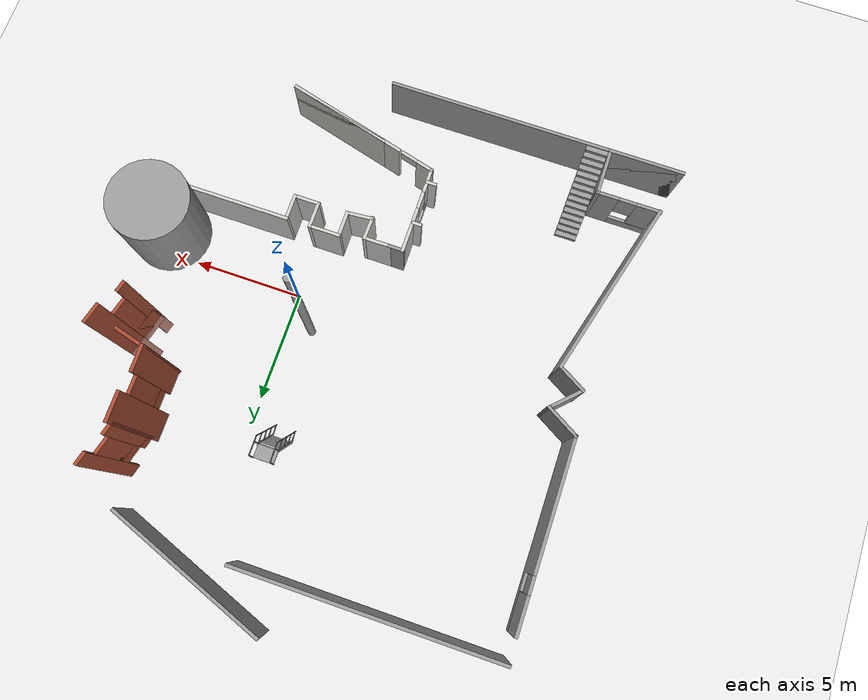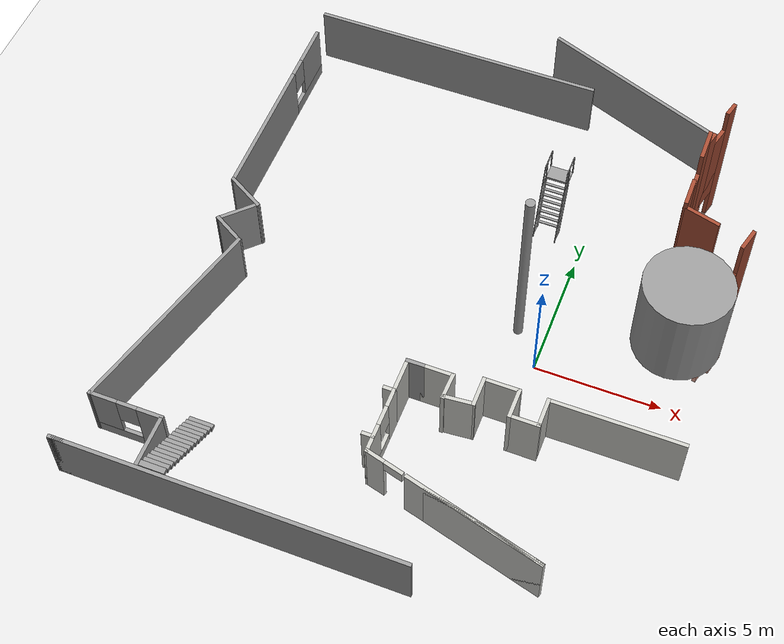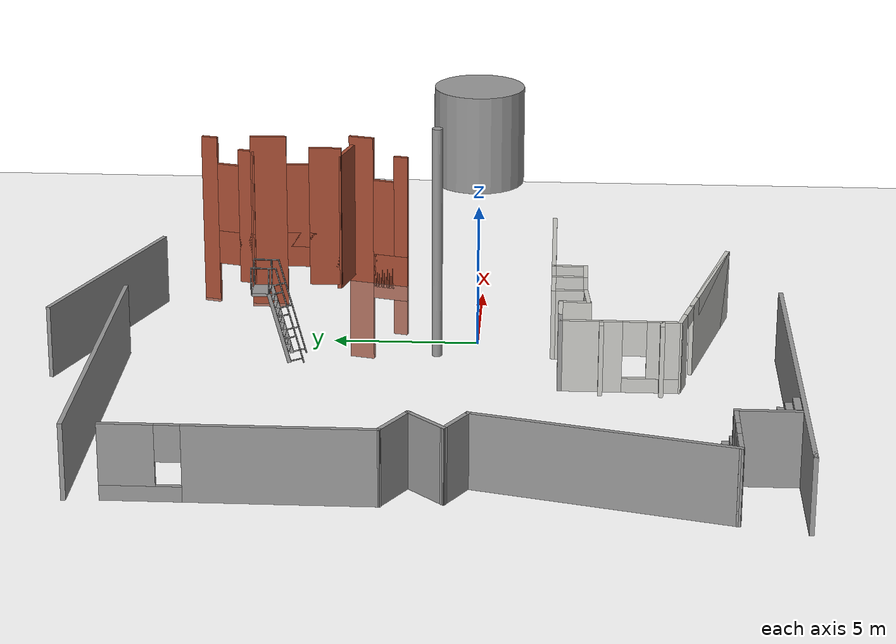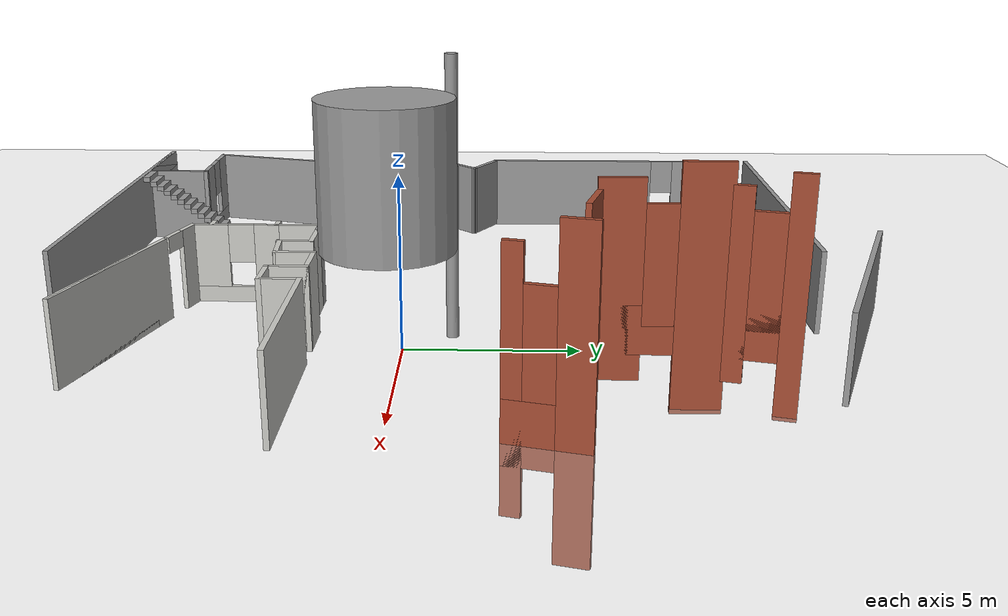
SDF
<sdf version="1.6">
 <world name="default">
  <light name="sun" type="directional">
   <pose>0 0 10 0 -0 0</pose>
   <diffuse>0.8 0.8 0.8 1</diffuse>
   <specular>0.1 0.1 0.1 1</specular>
   <attenuation>
    <range>1000</range>
    <constant>0.9</constant>
    <linear>0.01</linear>
    <quadratic>0.001</quadratic>
   </attenuation>
   <direction>-0.5 0.5 -1</direction>
  </light>
  <model name="ground_plane">
   <static>1</static>
   <link name="link">
    <collision name="collision">
     <geometry><plane><normal>0 0 1</normal><size>100 100</size></plane></geometry>
     <surface><friction><ode><mu>100</mu><mu2>50</mu2></ode></friction></surface>
    </collision>
    <visual name="visual">
     <cast_shadows>0</cast_shadows>
     <geometry><plane><normal>0 0 1</normal><size>100 100</size></plane></geometry>
     <material>
      <script><uri>file://media/materials/scripts/gazebo.material</uri><name>Gazebo/Grey</name></script>
     </material>
    </visual>
   </link>
  </model>
  <gravity>0 0 -9.8</gravity>
  <magnetic_field>6e-06 2.3e-05 -4.2e-05</magnetic_field>
  <atmosphere type="adiabatic"/>
  <physics name="default_physics" default="0" type="ode">
   <max_step_size>0.001</max_step_size>
   <real_time_factor>1</real_time_factor>
   <real_time_update_rate>1000</real_time_update_rate>
  </physics>
  <scene><ambient>0.4 0.4 0.4 1</ambient><background>0.7 0.7 0.7 1</background><shadows>1</shadows></scene>
  <spherical_coordinates>
   <surface_model>EARTH_WGS84</surface_model>
   <latitude_deg>0</latitude_deg>
   <longitude_deg>0</longitude_deg>
   <elevation>0</elevation>
   <heading_deg>0</heading_deg>
  </spherical_coordinates>
  <model name="ladder_75deg_2rails">
   <static>1</static>
   <link name="step0">
    <pose>0 0.071453 0.266667 0 -0 0</pose>
    <inertial>
     <mass>9.75482</mass>
     <inertia>
      <ixx>0.00957124</ixx>
      <iyy>0.65963</iyy>
      <izz>0.666842</izz>
      <ixy>0</ixy>
      <ixz>0</ixz>
      <iyz>0</iyz>
     </inertia>
    </inertial>
    <collision name="collision"><geometry><box><size>0.9 0.1016 0.0381</size></box></geometry></collision>
    <visual name="visual">
     <geometry><box><size>0.9 0.1016 0.0381</size></box></geometry>
     <material>
      <script><uri>file://media/materials/scripts/gazebo.material</uri><name>Gazebo/Grey</name></script>
     </material>
    </visual>
   </link>
   <link name="step1">
    <pose>0 0.142906 0.533333 0 -0 0</pose>
    <inertial>
     <mass>9.75482</mass>
     <inertia>
      <ixx>0.00957124</ixx>
      <iyy>0.65963</iyy>
      <izz>0.666842</izz>
      <ixy>0</ixy>
      <ixz>0</ixz>
      <iyz>0</iyz>
     </inertia>
    </inertial>
    <collision name="collision"><geometry><box><size>0.9 0.1016 0.0381</size></box></geometry></collision>
    <visual name="visual">
     <geometry><box><size>0.9 0.1016 0.0381</size></box></geometry>
     <material>
      <script><uri>file://media/materials/scripts/gazebo.material</uri><name>Gazebo/Grey</name></script>
     </material>
    </visual>
   </link>
   <link name="step2">
    <pose>0 0.214359 0.8 0 -0 0</pose>
    <inertial>
     <mass>9.75482</mass>
     <inertia>
      <ixx>0.00957124</ixx>
      <iyy>0.65963</iyy>
      <izz>0.666842</izz>
      <ixy>0</ixy>
      <ixz>0</ixz>
      <iyz>0</iyz>
     </inertia>
    </inertial>
    <collision name="collision"><geometry><box><size>0.9 0.1016 0.0381</size></box></geometry></collision>
    <visual name="visual">
     <geometry><box><size>0.9 0.1016 0.0381</size></box></geometry>
     <material>
      <script><uri>file://media/materials/scripts/gazebo.material</uri><name>Gazebo/Grey</name></script>
     </material>
    </visual>
   </link>
   <link name="step3">
    <pose>0 0.285812 1.06667 0 -0 0</pose>
    <inertial>
     <mass>9.75482</mass>
     <inertia>
      <ixx>0.00957124</ixx>
      <iyy>0.65963</iyy>
      <izz>0.666842</izz>
      <ixy>0</ixy>
      <ixz>0</ixz>
      <iyz>0</iyz>
     </inertia>
    </inertial>
    <collision name="collision"><geometry><box><size>0.9 0.1016 0.0381</size></box></geometry></collision>
    <visual name="visual">
     <geometry><box><size>0.9 0.1016 0.0381</size></box></geometry>
     <material>
      <script><uri>file://media/materials/scripts/gazebo.material</uri><name>Gazebo/Grey</name></script>
     </material>
    </visual>
   </link>
   <link name="step4">
    <pose>0 0.357266 1.33333 0 -0 0</pose>
    <inertial>
     <mass>9.75482</mass>
     <inertia>
      <ixx>0.00957124</ixx>
      <iyy>0.65963</iyy>
      <izz>0.666842</izz>
      <ixy>0</ixy>
      <ixz>0</ixz>
      <iyz>0</iyz>
     </inertia>
    </inertial>
    <collision name="collision"><geometry><box><size>0.9 0.1016 0.0381</size></box></geometry></collision>
    <visual name="visual">
     <geometry><box><size>0.9 0.1016 0.0381</size></box></geometry>
     <material>
      <script><uri>file://media/materials/scripts/gazebo.material</uri><name>Gazebo/Grey</name></script>
     </material>
    </visual>
   </link>
   <link name="step5">
    <pose>0 0.428719 1.6 0 -0 0</pose>
    <inertial>
     <mass>9.75482</mass>
     <inertia>
      <ixx>0.00957124</ixx>
      <iyy>0.65963</iyy>
      <izz>0.666842</izz>
      <ixy>0</ixy>
      <ixz>0</ixz>
      <iyz>0</iyz>
     </inertia>
    </inertial>
    <collision name="collision"><geometry><box><size>0.9 0.1016 0.0381</size></box></geometry></collision>
    <visual name="visual">
     <geometry><box><size>0.9 0.1016 0.0381</size></box></geometry>
     <material>
      <script><uri>file://media/materials/scripts/gazebo.material</uri><name>Gazebo/Grey</name></script>
     </material>
    </visual>
   </link>
   <link name="step6">
    <pose>0 0.500172 1.86667 0 -0 0</pose>
    <inertial>
     <mass>9.75482</mass>
     <inertia>
      <ixx>0.00957124</ixx>
      <iyy>0.65963</iyy>
      <izz>0.666842</izz>
      <ixy>0</ixy>
      <ixz>0</ixz>
      <iyz>0</iyz>
     </inertia>
    </inertial>
    <collision name="collision"><geometry><box><size>0.9 0.1016 0.0381</size></box></geometry></collision>
    <visual name="visual">
     <geometry><box><size>0.9 0.1016 0.0381</size></box></geometry>
     <material>
      <script><uri>file://media/materials/scripts/gazebo.material</uri><name>Gazebo/Grey</name></script>
     </material>
    </visual>
   </link>
   <link name="step7">
    <pose>0 0.571625 2.13333 0 -0 0</pose>
    <inertial>
     <mass>9.75482</mass>
     <inertia>
      <ixx>0.00957124</ixx>
      <iyy>0.65963</iyy>
      <izz>0.666842</izz>
      <ixy>0</ixy>
      <ixz>0</ixz>
      <iyz>0</iyz>
     </inertia>
    </inertial>
    <collision name="collision"><geometry><box><size>0.9 0.1016 0.0381</size></box></geometry></collision>
    <visual name="visual">
     <geometry><box><size>0.9 0.1016 0.0381</size></box></geometry>
     <material>
      <script><uri>file://media/materials/scripts/gazebo.material</uri><name>Gazebo/Grey</name></script>
     </material>
    </visual>
   </link>
   <link name="landing">
    <pose>0 0.943078 2.4 0 -0 0</pose>
    <inertial>
     <mass>57.6072</mass>
     <inertia><ixx>1.73518</ixx><iyy>3.89545</iyy><izz>5.6167</izz><ixy>0</ixy><ixz>0</ixz><iyz>0</iyz></inertia>
    </inertial>
    <collision name="collision"><geometry><box><size>0.9 0.6 0.1016</size></box></geometry></collision>
    <visual name="visual">
     <geometry><box><size>0.9 0.6 0.1016</size></box></geometry>
     <material>
      <script><uri>file://media/materials/scripts/gazebo.material</uri><name>Gazebo/Grey</name></script>
     </material>
    </visual>
   </link>
   <link name="left_side_wall">
    <pose>-0.45 0.321539 1.2 1.309 -0 0</pose>
    <collision name="collision"><geometry><box><size>0.0508 2.56466 0.13</size></box></geometry></collision>
    <visual name="visual">
     <geometry><box><size>0.0508 2.56466 0.13</size></box></geometry>
     <material>
      <script><uri>file://media/materials/scripts/gazebo.material</uri><name>Gazebo/Grey</name></script>
     </material>
    </visual>
   </link>
   <link name="right_side_wall">
    <pose>0.45 0.321539 1.2 1.309 -0 0</pose>
    <collision name="collision"><geometry><box><size>0.0508 2.56466 0.13</size></box></geometry></collision>
    <visual name="visual">
     <geometry><box><size>0.0508 2.56466 0.13</size></box></geometry>
     <material>
      <script><uri>file://media/materials/scripts/gazebo.material</uri><name>Gazebo/Grey</name></script>
     </material>
    </visual>
   </link>
   <link name="left_railing_long">
    <pose>-0.45 -0.053461 1.66651 -0.261799 0 0</pose>
    <collision name="collision">
     <geometry><cylinder><radius>0.02413</radius><length>3.51529</length></cylinder></geometry>
    </collision>
    <visual name="visual">
     <geometry><cylinder><radius>0.02413</radius><length>3.51529</length></cylinder></geometry>
     <material>
      <script><uri>file://media/materials/scripts/gazebo.material</uri><name>Gazebo/Grey</name></script>
     </material>
    </visual>
   </link>
   <link name="left_railing_upright0">
    <pose>-0.45 -0.210089 0.056293 1.309 -0 0</pose>
    <collision name="collision">
     <geometry><cylinder><radius>0.02413</radius><length>0.482963</length></cylinder></geometry>
    </collision>
    <visual name="visual">
     <geometry><cylinder><radius>0.02413</radius><length>0.482963</length></cylinder></geometry>
     <material>
      <script><uri>file://media/materials/scripts/gazebo.material</uri><name>Gazebo/Grey</name></script>
     </material>
    </visual>
   </link>
   <link name="left_railing_upright1">
    <pose>-0.45 0.00427 0.856293 1.309 -0 0</pose>
    <collision name="collision">
     <geometry><cylinder><radius>0.02413</radius><length>0.482963</length></cylinder></geometry>
    </collision>
    <visual name="visual">
     <geometry><cylinder><radius>0.02413</radius><length>0.482963</length></cylinder></geometry>
     <material>
      <script><uri>file://media/materials/scripts/gazebo.material</uri><name>Gazebo/Grey</name></script>
     </material>
    </visual>
   </link>
   <link name="left_railing_upright2">
    <pose>-0.45 0.21863 1.65629 1.309 -0 0</pose>
    <collision name="collision">
     <geometry><cylinder><radius>0.02413</radius><length>0.482963</length></cylinder></geometry>
    </collision>
    <visual name="visual">
     <geometry><cylinder><radius>0.02413</radius><length>0.482963</length></cylinder></geometry>
     <material>
      <script><uri>file://media/materials/scripts/gazebo.material</uri><name>Gazebo/Grey</name></script>
     </material>
    </visual>
   </link>
   <link name="left_railing_upright3">
    <pose>-0.45 0.432989 2.45629 1.309 -0 0</pose>
    <collision name="collision">
     <geometry><cylinder><radius>0.02413</radius><length>0.482963</length></cylinder></geometry>
    </collision>
    <visual name="visual">
     <geometry><cylinder><radius>0.02413</radius><length>0.482963</length></cylinder></geometry>
     <material>
      <script><uri>file://media/materials/scripts/gazebo.material</uri><name>Gazebo/Grey</name></script>
     </material>
    </visual>
   </link>
   <link name="left_railing_landing_top">
    <pose>-0.45 0.818078 3.35714 1.5708 -0 0</pose>
    <collision name="collision">
     <geometry><cylinder><radius>0.02413</radius><length>0.87413</length></cylinder></geometry>
    </collision>
    <visual name="visual">
     <geometry><cylinder><radius>0.02413</radius><length>0.87413</length></cylinder></geometry>
     <material>
      <script><uri>file://media/materials/scripts/gazebo.material</uri><name>Gazebo/Grey</name></script>
     </material>
    </visual>
   </link>
   <link name="left_railing_landing_upright_0">
    <pose>-0.45 0.643078 2.86651 0 -0 0</pose>
    <collision name="collision">
     <geometry><cylinder><radius>0.02413</radius><length>0.933013</length></cylinder></geometry>
    </collision>
    <visual name="visual">
     <geometry><cylinder><radius>0.02413</radius><length>0.933013</length></cylinder></geometry>
     <material>
      <script><uri>file://media/materials/scripts/gazebo.material</uri><name>Gazebo/Grey</name></script>
     </material>
    </visual>
   </link>
   <link name="left_railing_landing_upright_1">
    <pose>-0.45 1.24308 2.86651 0 -0 0</pose>
    <collision name="collision">
     <geometry><cylinder><radius>0.02413</radius><length>0.933013</length></cylinder></geometry>
    </collision>
    <visual name="visual">
     <geometry><cylinder><radius>0.02413</radius><length>0.933013</length></cylinder></geometry>
     <material>
      <script><uri>file://media/materials/scripts/gazebo.material</uri><name>Gazebo/Grey</name></script>
     </material>
    </visual>
   </link>
   <link name="right_railing_long">
    <pose>0.45 -0.053461 1.66651 -0.261799 0 0</pose>
    <collision name="collision">
     <geometry><cylinder><radius>0.02413</radius><length>3.51529</length></cylinder></geometry>
    </collision>
    <visual name="visual">
     <geometry><cylinder><radius>0.02413</radius><length>3.51529</length></cylinder></geometry>
     <material>
      <script><uri>file://media/materials/scripts/gazebo.material</uri><name>Gazebo/Grey</name></script>
     </material>
    </visual>
   </link>
   <link name="right_railing_upright0">
    <pose>0.45 -0.210089 0.056293 1.309 -0 0</pose>
    <collision name="collision">
     <geometry><cylinder><radius>0.02413</radius><length>0.482963</length></cylinder></geometry>
    </collision>
    <visual name="visual">
     <geometry><cylinder><radius>0.02413</radius><length>0.482963</length></cylinder></geometry>
     <material>
      <script><uri>file://media/materials/scripts/gazebo.material</uri><name>Gazebo/Grey</name></script>
     </material>
    </visual>
   </link>
   <link name="right_railing_upright1">
    <pose>0.45 0.00427 0.856293 1.309 -0 0</pose>
    <collision name="collision">
     <geometry><cylinder><radius>0.02413</radius><length>0.482963</length></cylinder></geometry>
    </collision>
    <visual name="visual">
     <geometry><cylinder><radius>0.02413</radius><length>0.482963</length></cylinder></geometry>
     <material>
      <script><uri>file://media/materials/scripts/gazebo.material</uri><name>Gazebo/Grey</name></script>
     </material>
    </visual>
   </link>
   <link name="right_railing_upright2">
    <pose>0.45 0.21863 1.65629 1.309 -0 0</pose>
    <collision name="collision">
     <geometry><cylinder><radius>0.02413</radius><length>0.482963</length></cylinder></geometry>
    </collision>
    <visual name="visual">
     <geometry><cylinder><radius>0.02413</radius><length>0.482963</length></cylinder></geometry>
     <material>
      <script><uri>file://media/materials/scripts/gazebo.material</uri><name>Gazebo/Grey</name></script>
     </material>
    </visual>
   </link>
   <link name="right_railing_upright3">
    <pose>0.45 0.432989 2.45629 1.309 -0 0</pose>
    <collision name="collision">
     <geometry><cylinder><radius>0.02413</radius><length>0.482963</length></cylinder></geometry>
    </collision>
    <visual name="visual">
     <geometry><cylinder><radius>0.02413</radius><length>0.482963</length></cylinder></geometry>
     <material>
      <script><uri>file://media/materials/scripts/gazebo.material</uri><name>Gazebo/Grey</name></script>
     </material>
    </visual>
   </link>
   <link name="right_railing_landing_top">
    <pose>0.45 0.818078 3.35714 1.5708 -0 0</pose>
    <collision name="collision">
     <geometry><cylinder><radius>0.02413</radius><length>0.87413</length></cylinder></geometry>
    </collision>
    <visual name="visual">
     <geometry><cylinder><radius>0.02413</radius><length>0.87413</length></cylinder></geometry>
     <material>
      <script><uri>file://media/materials/scripts/gazebo.material</uri><name>Gazebo/Grey</name></script>
     </material>
    </visual>
   </link>
   <link name="right_railing_landing_upright_0">
    <pose>0.45 0.643078 2.86651 0 -0 0</pose>
    <collision name="collision">
     <geometry><cylinder><radius>0.02413</radius><length>0.933013</length></cylinder></geometry>
    </collision>
    <visual name="visual">
     <geometry><cylinder><radius>0.02413</radius><length>0.933013</length></cylinder></geometry>
     <material>
      <script><uri>file://media/materials/scripts/gazebo.material</uri><name>Gazebo/Grey</name></script>
     </material>
    </visual>
   </link>
   <link name="right_railing_landing_upright_1">
    <pose>0.45 1.24308 2.86651 0 -0 0</pose>
    <collision name="collision">
     <geometry><cylinder><radius>0.02413</radius><length>0.933013</length></cylinder></geometry>
    </collision>
    <visual name="visual">
     <geometry><cylinder><radius>0.02413</radius><length>0.933013</length></cylinder></geometry>
     <material>
      <script><uri>file://media/materials/scripts/gazebo.material</uri><name>Gazebo/Grey</name></script>
     </material>
    </visual>
   </link>
   <pose>-1.56017 6.39658 0 0 -0 0</pose>
  </model>
  <model name="cierre_slaw_world_0">
   <link name="Stairs_0">
    <visual name="Stairs_0_Visual_0">
     <pose>-4.59466 -7.51518 0.083333 0 -0 0</pose>
     <geometry><box><size>1 0.233333 0.166667</size></box></geometry>
     <material>
      <script><uri>file://media/materials/scripts/gazebo.material</uri><name>Gazebo/Grey</name></script>
      <ambient>1 1 1 1</ambient>
      <diffuse>0.7 0.7 0.7 1</diffuse>
      <specular>0.01 0.01 0.01 1</specular>
      <emissive>0 0 0 1</emissive>
     </material>
    </visual>
    <visual name="Stairs_0_Visual_1">
     <pose>-4.59466 -7.74852 0.25 0 -0 0</pose>
     <geometry><box><size>1 0.233333 0.166667</size></box></geometry>
     <material>
      <script><uri>file://media/materials/scripts/gazebo.material</uri><name>Gazebo/Grey</name></script>
      <ambient>1 1 1 1</ambient>
      <diffuse>0.7 0.7 0.7 1</diffuse>
      <specular>0.01 0.01 0.01 1</specular>
      <emissive>0 0 0 1</emissive>
     </material>
    </visual>
    <visual name="Stairs_0_Visual_2">
     <pose>-4.59466 -7.98185 0.416667 0 -0 0</pose>
     <geometry><box><size>1 0.233333 0.166667</size></box></geometry>
     <material>
      <script><uri>file://media/materials/scripts/gazebo.material</uri><name>Gazebo/Grey</name></script>
      <ambient>1 1 1 1</ambient>
      <diffuse>0.7 0.7 0.7 1</diffuse>
      <specular>0.01 0.01 0.01 1</specular>
      <emissive>0 0 0 1</emissive>
     </material>
    </visual>
    <visual name="Stairs_0_Visual_3">
     <pose>-4.59466 -8.21518 0.583333 0 -0 0</pose>
     <geometry><box><size>1 0.233333 0.166667</size></box></geometry>
     <material>
      <script><uri>file://media/materials/scripts/gazebo.material</uri><name>Gazebo/Grey</name></script>
      <ambient>1 1 1 1</ambient>
      <diffuse>0.7 0.7 0.7 1</diffuse>
      <specular>0.01 0.01 0.01 1</specular>
      <emissive>0 0 0 1</emissive>
     </material>
    </visual>
    <visual name="Stairs_0_Visual_4">
     <pose>-4.59466 -8.44852 0.75 0 -0 0</pose>
     <geometry><box><size>1 0.233333 0.166667</size></box></geometry>
     <material>
      <script><uri>file://media/materials/scripts/gazebo.material</uri><name>Gazebo/Grey</name></script>
      <ambient>1 1 1 1</ambient>
      <diffuse>0.7 0.7 0.7 1</diffuse>
      <specular>0.01 0.01 0.01 1</specular>
      <emissive>0 0 0 1</emissive>
     </material>
    </visual>
    <visual name="Stairs_0_Visual_5">
     <pose>-4.59466 -8.68185 0.916667 0 -0 0</pose>
     <geometry><box><size>1 0.233333 0.166667</size></box></geometry>
     <material>
      <script><uri>file://media/materials/scripts/gazebo.material</uri><name>Gazebo/Grey</name></script>
      <ambient>1 1 1 1</ambient>
      <diffuse>0.7 0.7 0.7 1</diffuse>
      <specular>0.01 0.01 0.01 1</specular>
      <emissive>0 0 0 1</emissive>
     </material>
    </visual>
    <visual name="Stairs_0_Visual_6">
     <pose>-4.59466 -8.91518 1.08333 0 -0 0</pose>
     <geometry><box><size>1 0.233333 0.166667</size></box></geometry>
     <material>
      <script><uri>file://media/materials/scripts/gazebo.material</uri><name>Gazebo/Grey</name></script>
      <ambient>1 1 1 1</ambient>
      <diffuse>0.7 0.7 0.7 1</diffuse>
      <specular>0.01 0.01 0.01 1</specular>
      <emissive>0 0 0 1</emissive>
     </material>
    </visual>
    <visual name="Stairs_0_Visual_7">
     <pose>-4.59466 -9.14852 1.25 0 -0 0</pose>
     <geometry><box><size>1 0.233333 0.166667</size></box></geometry>
     <material>
      <script><uri>file://media/materials/scripts/gazebo.material</uri><name>Gazebo/Grey</name></script>
      <ambient>1 1 1 1</ambient>
      <diffuse>0.7 0.7 0.7 1</diffuse>
      <specular>0.01 0.01 0.01 1</specular>
      <emissive>0 0 0 1</emissive>
     </material>
    </visual>
    <visual name="Stairs_0_Visual_8">
     <pose>-4.59466 -9.38185 1.41667 0 -0 0</pose>
     <geometry><box><size>1 0.233333 0.166667</size></box></geometry>
     <material>
      <script><uri>file://media/materials/scripts/gazebo.material</uri><name>Gazebo/Grey</name></script>
      <ambient>1 1 1 1</ambient>
      <diffuse>0.7 0.7 0.7 1</diffuse>
      <specular>0.01 0.01 0.01 1</specular>
      <emissive>0 0 0 1</emissive>
     </material>
    </visual>
    <visual name="Stairs_0_Visual_9">
     <pose>-4.59466 -9.61518 1.58333 0 -0 0</pose>
     <geometry><box><size>1 0.233333 0.166667</size></box></geometry>
     <material>
      <script><uri>file://media/materials/scripts/gazebo.material</uri><name>Gazebo/Grey</name></script>
      <ambient>1 1 1 1</ambient>
      <diffuse>0.7 0.7 0.7 1</diffuse>
      <specular>0.01 0.01 0.01 1</specular>
      <emissive>0 0 0 1</emissive>
     </material>
    </visual>
    <visual name="Stairs_0_Visual_10">
     <pose>-4.59466 -9.84852 1.75 0 -0 0</pose>
     <geometry><box><size>1 0.233333 0.166667</size></box></geometry>
     <material>
      <script><uri>file://media/materials/scripts/gazebo.material</uri><name>Gazebo/Grey</name></script>
      <ambient>1 1 1 1</ambient>
      <diffuse>0.7 0.7 0.7 1</diffuse>
      <specular>0.01 0.01 0.01 1</specular>
      <emissive>0 0 0 1</emissive>
     </material>
    </visual>
    <visual name="Stairs_0_Visual_11">
     <pose>-4.59466 -10.0819 1.91667 0 -0 0</pose>
     <geometry><box><size>1 0.233333 0.166667</size></box></geometry>
     <material>
      <script><uri>file://media/materials/scripts/gazebo.material</uri><name>Gazebo/Grey</name></script>
      <ambient>1 1 1 1</ambient>
      <diffuse>0.7 0.7 0.7 1</diffuse>
      <specular>0.01 0.01 0.01 1</specular>
      <emissive>0 0 0 1</emissive>
     </material>
    </visual>
    <visual name="Stairs_0_Visual_12">
     <pose>-4.59466 -10.3152 2.08333 0 -0 0</pose>
     <geometry><box><size>1 0.233333 0.166667</size></box></geometry>
     <material>
      <script><uri>file://media/materials/scripts/gazebo.material</uri><name>Gazebo/Grey</name></script>
      <ambient>1 1 1 1</ambient>
      <diffuse>0.7 0.7 0.7 1</diffuse>
      <specular>0.01 0.01 0.01 1</specular>
      <emissive>0 0 0 1</emissive>
     </material>
    </visual>
    <visual name="Stairs_0_Visual_13">
     <pose>-4.59466 -10.5485 2.25 0 -0 0</pose>
     <geometry><box><size>1 0.233333 0.166667</size></box></geometry>
     <material>
      <script><uri>file://media/materials/scripts/gazebo.material</uri><name>Gazebo/Grey</name></script>
      <ambient>1 1 1 1</ambient>
      <diffuse>0.7 0.7 0.7 1</diffuse>
      <specular>0.01 0.01 0.01 1</specular>
      <emissive>0 0 0 1</emissive>
     </material>
    </visual>
    <visual name="Stairs_0_Visual_14">
     <pose>-4.59466 -10.7819 2.41667 0 -0 0</pose>
     <geometry><box><size>1 0.233333 0.166667</size></box></geometry>
     <material>
      <script><uri>file://media/materials/scripts/gazebo.material</uri><name>Gazebo/Grey</name></script>
      <ambient>1 1 1 1</ambient>
      <diffuse>0.7 0.7 0.7 1</diffuse>
      <specular>0.01 0.01 0.01 1</specular>
      <emissive>0 0 0 1</emissive>
     </material>
    </visual>
    <collision name="Stairs_0_Collision_0">
     <pose>-4.59466 -7.51518 0.083333 0 -0 0</pose>
     <geometry><box><size>1 0.233333 0.166667</size></box></geometry>
     <surface>
      <friction>
       <ode><mu>1</mu><mu2>1</mu2><fdir1>0 0 0</fdir1><slip1>0</slip1><slip2>0</slip2></ode>
       <torsional>
        <coefficient>1</coefficient>
        <patch_radius>0</patch_radius>
        <surface_radius>0</surface_radius>
        <use_patch_radius>1</use_patch_radius>
        <ode><slip>0</slip></ode>
       </torsional>
      </friction>
      <bounce><restitution_coefficient>0</restitution_coefficient><threshold>1e+06</threshold></bounce>
      <contact>
       <collide_without_contact>0</collide_without_contact>
       <collide_without_contact_bitmask>1</collide_without_contact_bitmask>
       <collide_bitmask>1</collide_bitmask>
       <ode>
        <soft_cfm>0</soft_cfm>
        <soft_erp>0.2</soft_erp>
        <kp>1e+13</kp>
        <kd>1</kd>
        <max_vel>0.01</max_vel>
        <min_depth>0</min_depth>
       </ode>
       <bullet>
        <split_impulse>1</split_impulse>
        <split_impulse_penetration_threshold>-0.01</split_impulse_penetration_threshold>
        <soft_cfm>0</soft_cfm>
        <soft_erp>0.2</soft_erp>
        <kp>1e+13</kp>
        <kd>1</kd>
       </bullet>
      </contact>
     </surface>
    </collision>
    <collision name="Stairs_0_Collision_1">
     <pose>-4.59466 -7.74852 0.25 0 -0 0</pose>
     <geometry><box><size>1 0.233333 0.166667</size></box></geometry>
     <surface>
      <friction>
       <ode><mu>1</mu><mu2>1</mu2><fdir1>0 0 0</fdir1><slip1>0</slip1><slip2>0</slip2></ode>
       <torsional>
        <coefficient>1</coefficient>
        <patch_radius>0</patch_radius>
        <surface_radius>0</surface_radius>
        <use_patch_radius>1</use_patch_radius>
        <ode><slip>0</slip></ode>
       </torsional>
      </friction>
      <bounce><restitution_coefficient>0</restitution_coefficient><threshold>1e+06</threshold></bounce>
      <contact>
       <collide_without_contact>0</collide_without_contact>
       <collide_without_contact_bitmask>1</collide_without_contact_bitmask>
       <collide_bitmask>1</collide_bitmask>
       <ode>
        <soft_cfm>0</soft_cfm>
        <soft_erp>0.2</soft_erp>
        <kp>1e+13</kp>
        <kd>1</kd>
        <max_vel>0.01</max_vel>
        <min_depth>0</min_depth>
       </ode>
       <bullet>
        <split_impulse>1</split_impulse>
        <split_impulse_penetration_threshold>-0.01</split_impulse_penetration_threshold>
        <soft_cfm>0</soft_cfm>
        <soft_erp>0.2</soft_erp>
        <kp>1e+13</kp>
        <kd>1</kd>
       </bullet>
      </contact>
     </surface>
    </collision>
    <collision name="Stairs_0_Collision_2">
     <pose>-4.59466 -7.98185 0.416667 0 -0 0</pose>
     <geometry><box><size>1 0.233333 0.166667</size></box></geometry>
     <surface>
      <friction>
       <ode><mu>1</mu><mu2>1</mu2><fdir1>0 0 0</fdir1><slip1>0</slip1><slip2>0</slip2></ode>
       <torsional>
        <coefficient>1</coefficient>
        <patch_radius>0</patch_radius>
        <surface_radius>0</surface_radius>
        <use_patch_radius>1</use_patch_radius>
        <ode><slip>0</slip></ode>
       </torsional>
      </friction>
      <bounce><restitution_coefficient>0</restitution_coefficient><threshold>1e+06</threshold></bounce>
      <contact>
       <collide_without_contact>0</collide_without_contact>
       <collide_without_contact_bitmask>1</collide_without_contact_bitmask>
       <collide_bitmask>1</collide_bitmask>
       <ode>
        <soft_cfm>0</soft_cfm>
        <soft_erp>0.2</soft_erp>
        <kp>1e+13</kp>
        <kd>1</kd>
        <max_vel>0.01</max_vel>
        <min_depth>0</min_depth>
       </ode>
       <bullet>
        <split_impulse>1</split_impulse>
        <split_impulse_penetration_threshold>-0.01</split_impulse_penetration_threshold>
        <soft_cfm>0</soft_cfm>
        <soft_erp>0.2</soft_erp>
        <kp>1e+13</kp>
        <kd>1</kd>
       </bullet>
      </contact>
     </surface>
    </collision>
    <collision name="Stairs_0_Collision_3">
     <pose>-4.59466 -8.21518 0.583333 0 -0 0</pose>
     <geometry><box><size>1 0.233333 0.166667</size></box></geometry>
     <surface>
      <friction>
       <ode><mu>1</mu><mu2>1</mu2><fdir1>0 0 0</fdir1><slip1>0</slip1><slip2>0</slip2></ode>
       <torsional>
        <coefficient>1</coefficient>
        <patch_radius>0</patch_radius>
        <surface_radius>0</surface_radius>
        <use_patch_radius>1</use_patch_radius>
        <ode><slip>0</slip></ode>
       </torsional>
      </friction>
      <bounce><restitution_coefficient>0</restitution_coefficient><threshold>1e+06</threshold></bounce>
      <contact>
       <collide_without_contact>0</collide_without_contact>
       <collide_without_contact_bitmask>1</collide_without_contact_bitmask>
       <collide_bitmask>1</collide_bitmask>
       <ode>
        <soft_cfm>0</soft_cfm>
        <soft_erp>0.2</soft_erp>
        <kp>1e+13</kp>
        <kd>1</kd>
        <max_vel>0.01</max_vel>
        <min_depth>0</min_depth>
       </ode>
       <bullet>
        <split_impulse>1</split_impulse>
        <split_impulse_penetration_threshold>-0.01</split_impulse_penetration_threshold>
        <soft_cfm>0</soft_cfm>
        <soft_erp>0.2</soft_erp>
        <kp>1e+13</kp>
        <kd>1</kd>
       </bullet>
      </contact>
     </surface>
    </collision>
    <collision name="Stairs_0_Collision_5">
     <pose>-4.59466 -8.68185 0.916667 0 -0 0</pose>
     <geometry><box><size>1 0.233333 0.166667</size></box></geometry>
     <surface>
      <friction>
       <ode><mu>1</mu><mu2>1</mu2><fdir1>0 0 0</fdir1><slip1>0</slip1><slip2>0</slip2></ode>
       <torsional>
        <coefficient>1</coefficient>
        <patch_radius>0</patch_radius>
        <surface_radius>0</surface_radius>
        <use_patch_radius>1</use_patch_radius>
        <ode><slip>0</slip></ode>
       </torsional>
      </friction>
      <bounce><restitution_coefficient>0</restitution_coefficient><threshold>1e+06</threshold></bounce>
      <contact>
       <collide_without_contact>0</collide_without_contact>
       <collide_without_contact_bitmask>1</collide_without_contact_bitmask>
       <collide_bitmask>1</collide_bitmask>
       <ode>
        <soft_cfm>0</soft_cfm>
        <soft_erp>0.2</soft_erp>
        <kp>1e+13</kp>
        <kd>1</kd>
        <max_vel>0.01</max_vel>
        <min_depth>0</min_depth>
       </ode>
       <bullet>
        <split_impulse>1</split_impulse>
        <split_impulse_penetration_threshold>-0.01</split_impulse_penetration_threshold>
        <soft_cfm>0</soft_cfm>
        <soft_erp>0.2</soft_erp>
        <kp>1e+13</kp>
        <kd>1</kd>
       </bullet>
      </contact>
     </surface>
    </collision>
    <collision name="Stairs_0_Collision_4">
     <pose>-4.59466 -8.44852 0.75 0 -0 0</pose>
     <geometry><box><size>1 0.233333 0.166667</size></box></geometry>
     <surface>
      <friction>
       <ode><mu>1</mu><mu2>1</mu2><fdir1>0 0 0</fdir1><slip1>0</slip1><slip2>0</slip2></ode>
       <torsional>
        <coefficient>1</coefficient>
        <patch_radius>0</patch_radius>
        <surface_radius>0</surface_radius>
        <use_patch_radius>1</use_patch_radius>
        <ode><slip>0</slip></ode>
       </torsional>
      </friction>
      <bounce><restitution_coefficient>0</restitution_coefficient><threshold>1e+06</threshold></bounce>
      <contact>
       <collide_without_contact>0</collide_without_contact>
       <collide_without_contact_bitmask>1</collide_without_contact_bitmask>
       <collide_bitmask>1</collide_bitmask>
       <ode>
        <soft_cfm>0</soft_cfm>
        <soft_erp>0.2</soft_erp>
        <kp>1e+13</kp>
        <kd>1</kd>
        <max_vel>0.01</max_vel>
        <min_depth>0</min_depth>
       </ode>
       <bullet>
        <split_impulse>1</split_impulse>
        <split_impulse_penetration_threshold>-0.01</split_impulse_penetration_threshold>
        <soft_cfm>0</soft_cfm>
        <soft_erp>0.2</soft_erp>
        <kp>1e+13</kp>
        <kd>1</kd>
       </bullet>
      </contact>
     </surface>
    </collision>
    <collision name="Stairs_0_Collision_6">
     <pose>-4.59466 -8.91518 1.08333 0 -0 0</pose>
     <geometry><box><size>1 0.233333 0.166667</size></box></geometry>
     <surface>
      <friction>
       <ode><mu>1</mu><mu2>1</mu2><fdir1>0 0 0</fdir1><slip1>0</slip1><slip2>0</slip2></ode>
       <torsional>
        <coefficient>1</coefficient>
        <patch_radius>0</patch_radius>
        <surface_radius>0</surface_radius>
        <use_patch_radius>1</use_patch_radius>
        <ode><slip>0</slip></ode>
       </torsional>
      </friction>
      <bounce><restitution_coefficient>0</restitution_coefficient><threshold>1e+06</threshold></bounce>
      <contact>
       <collide_without_contact>0</collide_without_contact>
       <collide_without_contact_bitmask>1</collide_without_contact_bitmask>
       <collide_bitmask>1</collide_bitmask>
       <ode>
        <soft_cfm>0</soft_cfm>
        <soft_erp>0.2</soft_erp>
        <kp>1e+13</kp>
        <kd>1</kd>
        <max_vel>0.01</max_vel>
        <min_depth>0</min_depth>
       </ode>
       <bullet>
        <split_impulse>1</split_impulse>
        <split_impulse_penetration_threshold>-0.01</split_impulse_penetration_threshold>
        <soft_cfm>0</soft_cfm>
        <soft_erp>0.2</soft_erp>
        <kp>1e+13</kp>
        <kd>1</kd>
       </bullet>
      </contact>
     </surface>
    </collision>
    <collision name="Stairs_0_Collision_7">
     <pose>-4.59466 -9.14852 1.25 0 -0 0</pose>
     <geometry><box><size>1 0.233333 0.166667</size></box></geometry>
     <surface>
      <friction>
       <ode><mu>1</mu><mu2>1</mu2><fdir1>0 0 0</fdir1><slip1>0</slip1><slip2>0</slip2></ode>
       <torsional>
        <coefficient>1</coefficient>
        <patch_radius>0</patch_radius>
        <surface_radius>0</surface_radius>
        <use_patch_radius>1</use_patch_radius>
        <ode><slip>0</slip></ode>
       </torsional>
      </friction>
      <bounce><restitution_coefficient>0</restitution_coefficient><threshold>1e+06</threshold></bounce>
      <contact>
       <collide_without_contact>0</collide_without_contact>
       <collide_without_contact_bitmask>1</collide_without_contact_bitmask>
       <collide_bitmask>1</collide_bitmask>
       <ode>
        <soft_cfm>0</soft_cfm>
        <soft_erp>0.2</soft_erp>
        <kp>1e+13</kp>
        <kd>1</kd>
        <max_vel>0.01</max_vel>
        <min_depth>0</min_depth>
       </ode>
       <bullet>
        <split_impulse>1</split_impulse>
        <split_impulse_penetration_threshold>-0.01</split_impulse_penetration_threshold>
        <soft_cfm>0</soft_cfm>
        <soft_erp>0.2</soft_erp>
        <kp>1e+13</kp>
        <kd>1</kd>
       </bullet>
      </contact>
     </surface>
    </collision>
    <collision name="Stairs_0_Collision_8">
     <pose>-4.59466 -9.38185 1.41667 0 -0 0</pose>
     <geometry><box><size>1 0.233333 0.166667</size></box></geometry>
     <surface>
      <friction>
       <ode><mu>1</mu><mu2>1</mu2><fdir1>0 0 0</fdir1><slip1>0</slip1><slip2>0</slip2></ode>
       <torsional>
        <coefficient>1</coefficient>
        <patch_radius>0</patch_radius>
        <surface_radius>0</surface_radius>
        <use_patch_radius>1</use_patch_radius>
        <ode><slip>0</slip></ode>
       </torsional>
      </friction>
      <bounce><restitution_coefficient>0</restitution_coefficient><threshold>1e+06</threshold></bounce>
      <contact>
       <collide_without_contact>0</collide_without_contact>
       <collide_without_contact_bitmask>1</collide_without_contact_bitmask>
       <collide_bitmask>1</collide_bitmask>
       <ode>
        <soft_cfm>0</soft_cfm>
        <soft_erp>0.2</soft_erp>
        <kp>1e+13</kp>
        <kd>1</kd>
        <max_vel>0.01</max_vel>
        <min_depth>0</min_depth>
       </ode>
       <bullet>
        <split_impulse>1</split_impulse>
        <split_impulse_penetration_threshold>-0.01</split_impulse_penetration_threshold>
        <soft_cfm>0</soft_cfm>
        <soft_erp>0.2</soft_erp>
        <kp>1e+13</kp>
        <kd>1</kd>
       </bullet>
      </contact>
     </surface>
    </collision>
    <collision name="Stairs_0_Collision_9">
     <pose>-4.59466 -9.61518 1.58333 0 -0 0</pose>
     <geometry><box><size>1 0.233333 0.166667</size></box></geometry>
     <surface>
      <friction>
       <ode><mu>1</mu><mu2>1</mu2><fdir1>0 0 0</fdir1><slip1>0</slip1><slip2>0</slip2></ode>
       <torsional>
        <coefficient>1</coefficient>
        <patch_radius>0</patch_radius>
        <surface_radius>0</surface_radius>
        <use_patch_radius>1</use_patch_radius>
        <ode><slip>0</slip></ode>
       </torsional>
      </friction>
      <bounce><restitution_coefficient>0</restitution_coefficient><threshold>1e+06</threshold></bounce>
      <contact>
       <collide_without_contact>0</collide_without_contact>
       <collide_without_contact_bitmask>1</collide_without_contact_bitmask>
       <collide_bitmask>1</collide_bitmask>
       <ode>
        <soft_cfm>0</soft_cfm>
        <soft_erp>0.2</soft_erp>
        <kp>1e+13</kp>
        <kd>1</kd>
        <max_vel>0.01</max_vel>
        <min_depth>0</min_depth>
       </ode>
       <bullet>
        <split_impulse>1</split_impulse>
        <split_impulse_penetration_threshold>-0.01</split_impulse_penetration_threshold>
        <soft_cfm>0</soft_cfm>
        <soft_erp>0.2</soft_erp>
        <kp>1e+13</kp>
        <kd>1</kd>
       </bullet>
      </contact>
     </surface>
    </collision>
    <collision name="Stairs_0_Collision_10">
     <pose>-4.59466 -9.84852 1.75 0 -0 0</pose>
     <geometry><box><size>1 0.233333 0.166667</size></box></geometry>
     <surface>
      <friction>
       <ode><mu>1</mu><mu2>1</mu2><fdir1>0 0 0</fdir1><slip1>0</slip1><slip2>0</slip2></ode>
       <torsional>
        <coefficient>1</coefficient>
        <patch_radius>0</patch_radius>
        <surface_radius>0</surface_radius>
        <use_patch_radius>1</use_patch_radius>
        <ode><slip>0</slip></ode>
       </torsional>
      </friction>
      <bounce><restitution_coefficient>0</restitution_coefficient><threshold>1e+06</threshold></bounce>
      <contact>
       <collide_without_contact>0</collide_without_contact>
       <collide_without_contact_bitmask>1</collide_without_contact_bitmask>
       <collide_bitmask>1</collide_bitmask>
       <ode>
        <soft_cfm>0</soft_cfm>
        <soft_erp>0.2</soft_erp>
        <kp>1e+13</kp>
        <kd>1</kd>
        <max_vel>0.01</max_vel>
        <min_depth>0</min_depth>
       </ode>
       <bullet>
        <split_impulse>1</split_impulse>
        <split_impulse_penetration_threshold>-0.01</split_impulse_penetration_threshold>
        <soft_cfm>0</soft_cfm>
        <soft_erp>0.2</soft_erp>
        <kp>1e+13</kp>
        <kd>1</kd>
       </bullet>
      </contact>
     </surface>
    </collision>
    <collision name="Stairs_0_Collision_13">
     <pose>-4.59466 -10.5485 2.25 0 -0 0</pose>
     <geometry><box><size>1 0.233333 0.166667</size></box></geometry>
     <surface>
      <friction>
       <ode><mu>1</mu><mu2>1</mu2><fdir1>0 0 0</fdir1><slip1>0</slip1><slip2>0</slip2></ode>
       <torsional>
        <coefficient>1</coefficient>
        <patch_radius>0</patch_radius>
        <surface_radius>0</surface_radius>
        <use_patch_radius>1</use_patch_radius>
        <ode><slip>0</slip></ode>
       </torsional>
      </friction>
      <bounce><restitution_coefficient>0</restitution_coefficient><threshold>1e+06</threshold></bounce>
      <contact>
       <collide_without_contact>0</collide_without_contact>
       <collide_without_contact_bitmask>1</collide_without_contact_bitmask>
       <collide_bitmask>1</collide_bitmask>
       <ode>
        <soft_cfm>0</soft_cfm>
        <soft_erp>0.2</soft_erp>
        <kp>1e+13</kp>
        <kd>1</kd>
        <max_vel>0.01</max_vel>
        <min_depth>0</min_depth>
       </ode>
       <bullet>
        <split_impulse>1</split_impulse>
        <split_impulse_penetration_threshold>-0.01</split_impulse_penetration_threshold>
        <soft_cfm>0</soft_cfm>
        <soft_erp>0.2</soft_erp>
        <kp>1e+13</kp>
        <kd>1</kd>
       </bullet>
      </contact>
     </surface>
    </collision>
    <collision name="Stairs_0_Collision_11">
     <pose>-4.59466 -10.0819 1.91667 0 -0 0</pose>
     <geometry><box><size>1 0.233333 0.166667</size></box></geometry>
     <surface>
      <friction>
       <ode><mu>1</mu><mu2>1</mu2><fdir1>0 0 0</fdir1><slip1>0</slip1><slip2>0</slip2></ode>
       <torsional>
        <coefficient>1</coefficient>
        <patch_radius>0</patch_radius>
        <surface_radius>0</surface_radius>
        <use_patch_radius>1</use_patch_radius>
        <ode><slip>0</slip></ode>
       </torsional>
      </friction>
      <bounce><restitution_coefficient>0</restitution_coefficient><threshold>1e+06</threshold></bounce>
      <contact>
       <collide_without_contact>0</collide_without_contact>
       <collide_without_contact_bitmask>1</collide_without_contact_bitmask>
       <collide_bitmask>1</collide_bitmask>
       <ode>
        <soft_cfm>0</soft_cfm>
        <soft_erp>0.2</soft_erp>
        <kp>1e+13</kp>
        <kd>1</kd>
        <max_vel>0.01</max_vel>
        <min_depth>0</min_depth>
       </ode>
       <bullet>
        <split_impulse>1</split_impulse>
        <split_impulse_penetration_threshold>-0.01</split_impulse_penetration_threshold>
        <soft_cfm>0</soft_cfm>
        <soft_erp>0.2</soft_erp>
        <kp>1e+13</kp>
        <kd>1</kd>
       </bullet>
      </contact>
     </surface>
    </collision>
    <collision name="Stairs_0_Collision_12">
     <pose>-4.59466 -10.3152 2.08333 0 -0 0</pose>
     <geometry><box><size>1 0.233333 0.166667</size></box></geometry>
     <surface>
      <friction>
       <ode><mu>1</mu><mu2>1</mu2><fdir1>0 0 0</fdir1><slip1>0</slip1><slip2>0</slip2></ode>
       <torsional>
        <coefficient>1</coefficient>
        <patch_radius>0</patch_radius>
        <surface_radius>0</surface_radius>
        <use_patch_radius>1</use_patch_radius>
        <ode><slip>0</slip></ode>
       </torsional>
      </friction>
      <bounce><restitution_coefficient>0</restitution_coefficient><threshold>1e+06</threshold></bounce>
      <contact>
       <collide_without_contact>0</collide_without_contact>
       <collide_without_contact_bitmask>1</collide_without_contact_bitmask>
       <collide_bitmask>1</collide_bitmask>
       <ode>
        <soft_cfm>0</soft_cfm>
        <soft_erp>0.2</soft_erp>
        <kp>1e+13</kp>
        <kd>1</kd>
        <max_vel>0.01</max_vel>
        <min_depth>0</min_depth>
       </ode>
       <bullet>
        <split_impulse>1</split_impulse>
        <split_impulse_penetration_threshold>-0.01</split_impulse_penetration_threshold>
        <soft_cfm>0</soft_cfm>
        <soft_erp>0.2</soft_erp>
        <kp>1e+13</kp>
        <kd>1</kd>
       </bullet>
      </contact>
     </surface>
    </collision>
    <collision name="Stairs_0_Collision_14">
     <pose>-4.59466 -10.7819 2.41667 0 -0 0</pose>
     <geometry><box><size>1 0.233333 0.166667</size></box></geometry>
     <surface>
      <friction>
       <ode><mu>1</mu><mu2>1</mu2><fdir1>0 0 0</fdir1><slip1>0</slip1><slip2>0</slip2></ode>
       <torsional>
        <coefficient>1</coefficient>
        <patch_radius>0</patch_radius>
        <surface_radius>0</surface_radius>
        <use_patch_radius>1</use_patch_radius>
        <ode><slip>0</slip></ode>
       </torsional>
      </friction>
      <bounce><restitution_coefficient>0</restitution_coefficient><threshold>1e+06</threshold></bounce>
      <contact>
       <collide_without_contact>0</collide_without_contact>
       <collide_without_contact_bitmask>1</collide_without_contact_bitmask>
       <collide_bitmask>1</collide_bitmask>
       <ode>
        <soft_cfm>0</soft_cfm>
        <soft_erp>0.2</soft_erp>
        <kp>1e+13</kp>
        <kd>1</kd>
        <max_vel>0.01</max_vel>
        <min_depth>0</min_depth>
       </ode>
       <bullet>
        <split_impulse>1</split_impulse>
        <split_impulse_penetration_threshold>-0.01</split_impulse_penetration_threshold>
        <soft_cfm>0</soft_cfm>
        <soft_erp>0.2</soft_erp>
        <kp>1e+13</kp>
        <kd>1</kd>
       </bullet>
      </contact>
     </surface>
    </collision>
   </link>
   <link name="Wall_23">
    <pose>-6.85744 -10.9944 0 0 -0 0</pose>
    <visual name="Wall_23_Visual">
     <pose>0 0 1.25 0 -0 0</pose>
     <geometry><box><size>3.5 0.15 2.5</size></box></geometry>
     <material>
      <script><uri>file://media/materials/scripts/gazebo.material</uri><name>Gazebo/Grey</name></script>
      <ambient>1 1 1 1</ambient>
      <diffuse>0.7 0.7 0.7 1</diffuse>
      <specular>0.01 0.01 0.01 1</specular>
      <emissive>0 0 0 1</emissive>
     </material>
    </visual>
    <collision name="Wall_23_Collision">
     <pose>0 0 1.25 0 -0 0</pose>
     <geometry><box><size>3.5 0.15 2.5</size></box></geometry>
     <surface>
      <friction>
       <ode><mu>1</mu><mu2>1</mu2><fdir1>0 0 0</fdir1><slip1>0</slip1><slip2>0</slip2></ode>
       <torsional>
        <coefficient>1</coefficient>
        <patch_radius>0</patch_radius>
        <surface_radius>0</surface_radius>
        <use_patch_radius>1</use_patch_radius>
        <ode><slip>0</slip></ode>
       </torsional>
      </friction>
      <bounce><restitution_coefficient>0</restitution_coefficient><threshold>1e+06</threshold></bounce>
      <contact>
       <collide_without_contact>0</collide_without_contact>
       <collide_without_contact_bitmask>1</collide_without_contact_bitmask>
       <collide_bitmask>1</collide_bitmask>
       <ode>
        <soft_cfm>0</soft_cfm>
        <soft_erp>0.2</soft_erp>
        <kp>1e+13</kp>
        <kd>1</kd>
        <max_vel>0.01</max_vel>
        <min_depth>0</min_depth>
       </ode>
       <bullet>
        <split_impulse>1</split_impulse>
        <split_impulse_penetration_threshold>-0.01</split_impulse_penetration_threshold>
        <soft_cfm>0</soft_cfm>
        <soft_erp>0.2</soft_erp>
        <kp>1e+13</kp>
        <kd>1</kd>
       </bullet>
      </contact>
     </surface>
    </collision>
   </link>
   <link name="Wall_24">
    <pose>-5.18244 -9.94435 0 0 -0 1.5708</pose>
    <visual name="Wall_24_Visual">
     <pose>0 0 1.25 0 -0 0</pose>
     <geometry><box><size>2.25 0.15 2.5</size></box></geometry>
     <material>
      <script><uri>file://media/materials/scripts/gazebo.material</uri><name>Gazebo/Grey</name></script>
      <ambient>1 1 1 1</ambient>
      <diffuse>0.7 0.7 0.7 1</diffuse>
      <specular>0.01 0.01 0.01 1</specular>
      <emissive>0 0 0 1</emissive>
     </material>
    </visual>
    <collision name="Wall_24_Collision">
     <pose>0 0 1.25 0 -0 0</pose>
     <geometry><box><size>2.25 0.15 2.5</size></box></geometry>
     <surface>
      <friction>
       <ode><mu>1</mu><mu2>1</mu2><fdir1>0 0 0</fdir1><slip1>0</slip1><slip2>0</slip2></ode>
       <torsional>
        <coefficient>1</coefficient>
        <patch_radius>0</patch_radius>
        <surface_radius>0</surface_radius>
        <use_patch_radius>1</use_patch_radius>
        <ode><slip>0</slip></ode>
       </torsional>
      </friction>
      <bounce><restitution_coefficient>0</restitution_coefficient><threshold>1e+06</threshold></bounce>
      <contact>
       <collide_without_contact>0</collide_without_contact>
       <collide_without_contact_bitmask>1</collide_without_contact_bitmask>
       <collide_bitmask>1</collide_bitmask>
       <ode>
        <soft_cfm>0</soft_cfm>
        <soft_erp>0.2</soft_erp>
        <kp>1e+13</kp>
        <kd>1</kd>
        <max_vel>0.01</max_vel>
        <min_depth>0</min_depth>
       </ode>
       <bullet>
        <split_impulse>1</split_impulse>
        <split_impulse_penetration_threshold>-0.01</split_impulse_penetration_threshold>
        <soft_cfm>0</soft_cfm>
        <soft_erp>0.2</soft_erp>
        <kp>1e+13</kp>
        <kd>1</kd>
       </bullet>
      </contact>
     </surface>
    </collision>
   </link>
   <link name="Wall_25">
    <pose>-6.60744 -8.89435 0 0 -0 3.14159</pose>
    <visual name="Wall_25_Visual_0">
     <pose>-0.971946 0 1.25 0 -0 0</pose>
     <geometry><box><size>1.05611 0.15 2.5</size></box></geometry>
     <material>
      <script><uri>file://media/materials/scripts/gazebo.material</uri><name>Gazebo/Grey</name></script>
      <ambient>1 1 1 1</ambient>
      <diffuse>0.7 0.7 0.7 1</diffuse>
      <specular>0.01 0.01 0.01 1</specular>
      <emissive>0 0 0 1</emissive>
     </material>
    </visual>
    <visual name="Wall_25_Visual_1">
     <pose>0.528054 0 0.25 0 -0 0</pose>
     <geometry><box><size>1.94389 0.15 0.5</size></box></geometry>
     <material>
      <script><uri>file://media/materials/scripts/gazebo.material</uri><name>Gazebo/Grey</name></script>
      <ambient>1 1 1 1</ambient>
      <diffuse>0.7 0.7 0.7 1</diffuse>
      <specular>0.01 0.01 0.01 1</specular>
      <emissive>0 0 0 1</emissive>
     </material>
    </visual>
    <visual name="Wall_25_Visual_2">
     <pose>0.928054 0 1.5 0 -0 0</pose>
     <geometry><box><size>1.14389 0.15 2</size></box></geometry>
     <material>
      <script><uri>file://media/materials/scripts/gazebo.material</uri><name>Gazebo/Grey</name></script>
      <ambient>1 1 1 1</ambient>
      <diffuse>0.7 0.7 0.7 1</diffuse>
      <specular>0.01 0.01 0.01 1</specular>
      <emissive>0 0 0 1</emissive>
     </material>
    </visual>
    <visual name="Wall_25_Visual_3">
     <pose>-0.043892 0 1.9 0 -0 0</pose>
     <geometry><box><size>0.8 0.15 1.2</size></box></geometry>
     <material>
      <script><uri>file://media/materials/scripts/gazebo.material</uri><name>Gazebo/Grey</name></script>
      <ambient>1 1 1 1</ambient>
      <diffuse>0.7 0.7 0.7 1</diffuse>
      <specular>0.01 0.01 0.01 1</specular>
      <emissive>0 0 0 1</emissive>
     </material>
    </visual>
    <collision name="Wall_25_Collision_0">
     <pose>-0.971946 0 1.25 0 -0 0</pose>
     <geometry><box><size>1.05611 0.15 2.5</size></box></geometry>
     <surface>
      <friction>
       <ode><mu>1</mu><mu2>1</mu2><fdir1>0 0 0</fdir1><slip1>0</slip1><slip2>0</slip2></ode>
       <torsional>
        <coefficient>1</coefficient>
        <patch_radius>0</patch_radius>
        <surface_radius>0</surface_radius>
        <use_patch_radius>1</use_patch_radius>
        <ode><slip>0</slip></ode>
       </torsional>
      </friction>
      <bounce><restitution_coefficient>0</restitution_coefficient><threshold>1e+06</threshold></bounce>
      <contact>
       <collide_without_contact>0</collide_without_contact>
       <collide_without_contact_bitmask>1</collide_without_contact_bitmask>
       <collide_bitmask>1</collide_bitmask>
       <ode>
        <soft_cfm>0</soft_cfm>
        <soft_erp>0.2</soft_erp>
        <kp>1e+13</kp>
        <kd>1</kd>
        <max_vel>0.01</max_vel>
        <min_depth>0</min_depth>
       </ode>
       <bullet>
        <split_impulse>1</split_impulse>
        <split_impulse_penetration_threshold>-0.01</split_impulse_penetration_threshold>
        <soft_cfm>0</soft_cfm>
        <soft_erp>0.2</soft_erp>
        <kp>1e+13</kp>
        <kd>1</kd>
       </bullet>
      </contact>
     </surface>
    </collision>
    <collision name="Wall_25_Collision_1">
     <pose>0.528054 0 0.25 0 -0 0</pose>
     <geometry><box><size>1.94389 0.15 0.5</size></box></geometry>
     <surface>
      <friction>
       <ode><mu>1</mu><mu2>1</mu2><fdir1>0 0 0</fdir1><slip1>0</slip1><slip2>0</slip2></ode>
       <torsional>
        <coefficient>1</coefficient>
        <patch_radius>0</patch_radius>
        <surface_radius>0</surface_radius>
        <use_patch_radius>1</use_patch_radius>
        <ode><slip>0</slip></ode>
       </torsional>
      </friction>
      <bounce><restitution_coefficient>0</restitution_coefficient><threshold>1e+06</threshold></bounce>
      <contact>
       <collide_without_contact>0</collide_without_contact>
       <collide_without_contact_bitmask>1</collide_without_contact_bitmask>
       <collide_bitmask>1</collide_bitmask>
       <ode>
        <soft_cfm>0</soft_cfm>
        <soft_erp>0.2</soft_erp>
        <kp>1e+13</kp>
        <kd>1</kd>
        <max_vel>0.01</max_vel>
        <min_depth>0</min_depth>
       </ode>
       <bullet>
        <split_impulse>1</split_impulse>
        <split_impulse_penetration_threshold>-0.01</split_impulse_penetration_threshold>
        <soft_cfm>0</soft_cfm>
        <soft_erp>0.2</soft_erp>
        <kp>1e+13</kp>
        <kd>1</kd>
       </bullet>
      </contact>
     </surface>
    </collision>
    <collision name="Wall_25_Collision_2">
     <pose>0.928054 0 1.5 0 -0 0</pose>
     <geometry><box><size>1.14389 0.15 2</size></box></geometry>
     <surface>
      <friction>
       <ode><mu>1</mu><mu2>1</mu2><fdir1>0 0 0</fdir1><slip1>0</slip1><slip2>0</slip2></ode>
       <torsional>
        <coefficient>1</coefficient>
        <patch_radius>0</patch_radius>
        <surface_radius>0</surface_radius>
        <use_patch_radius>1</use_patch_radius>
        <ode><slip>0</slip></ode>
       </torsional>
      </friction>
      <bounce><restitution_coefficient>0</restitution_coefficient><threshold>1e+06</threshold></bounce>
      <contact>
       <collide_without_contact>0</collide_without_contact>
       <collide_without_contact_bitmask>1</collide_without_contact_bitmask>
       <collide_bitmask>1</collide_bitmask>
       <ode>
        <soft_cfm>0</soft_cfm>
        <soft_erp>0.2</soft_erp>
        <kp>1e+13</kp>
        <kd>1</kd>
        <max_vel>0.01</max_vel>
        <min_depth>0</min_depth>
       </ode>
       <bullet>
        <split_impulse>1</split_impulse>
        <split_impulse_penetration_threshold>-0.01</split_impulse_penetration_threshold>
        <soft_cfm>0</soft_cfm>
        <soft_erp>0.2</soft_erp>
        <kp>1e+13</kp>
        <kd>1</kd>
       </bullet>
      </contact>
     </surface>
    </collision>
    <collision name="Wall_25_Collision_3">
     <pose>-0.043892 0 1.9 0 -0 0</pose>
     <geometry><box><size>0.8 0.15 1.2</size></box></geometry>
     <surface>
      <friction>
       <ode><mu>1</mu><mu2>1</mu2><fdir1>0 0 0</fdir1><slip1>0</slip1><slip2>0</slip2></ode>
       <torsional>
        <coefficient>1</coefficient>
        <patch_radius>0</patch_radius>
        <surface_radius>0</surface_radius>
        <use_patch_radius>1</use_patch_radius>
        <ode><slip>0</slip></ode>
       </torsional>
      </friction>
      <bounce><restitution_coefficient>0</restitution_coefficient><threshold>1e+06</threshold></bounce>
      <contact>
       <collide_without_contact>0</collide_without_contact>
       <collide_without_contact_bitmask>1</collide_without_contact_bitmask>
       <collide_bitmask>1</collide_bitmask>
       <ode>
        <soft_cfm>0</soft_cfm>
        <soft_erp>0.2</soft_erp>
        <kp>1e+13</kp>
        <kd>1</kd>
        <max_vel>0.01</max_vel>
        <min_depth>0</min_depth>
       </ode>
       <bullet>
        <split_impulse>1</split_impulse>
        <split_impulse_penetration_threshold>-0.01</split_impulse_penetration_threshold>
        <soft_cfm>0</soft_cfm>
        <soft_erp>0.2</soft_erp>
        <kp>1e+13</kp>
        <kd>1</kd>
       </bullet>
      </contact>
     </surface>
    </collision>
   </link>
   <link name="Wall_26">
    <pose>-6.95187 -4.86161 0 0 -0 1.309</pose>
    <visual name="Wall_26_Visual">
     <pose>0 0 1.25 0 -0 0</pose>
     <geometry><box><size>8.5 0.15 2.5</size></box></geometry>
     <material>
      <script><uri>file://media/materials/scripts/gazebo.material</uri><name>Gazebo/Grey</name></script>
      <ambient>1 1 1 1</ambient>
      <diffuse>0.7 0.7 0.7 1</diffuse>
      <specular>0.01 0.01 0.01 1</specular>
      <emissive>0 0 0 1</emissive>
     </material>
    </visual>
    <collision name="Wall_26_Collision">
     <pose>0 0 1.25 0 -0 0</pose>
     <geometry><box><size>8.5 0.15 2.5</size></box></geometry>
     <surface>
      <friction>
       <ode><mu>1</mu><mu2>1</mu2><fdir1>0 0 0</fdir1><slip1>0</slip1><slip2>0</slip2></ode>
       <torsional>
        <coefficient>1</coefficient>
        <patch_radius>0</patch_radius>
        <surface_radius>0</surface_radius>
        <use_patch_radius>1</use_patch_radius>
        <ode><slip>0</slip></ode>
       </torsional>
      </friction>
      <bounce><restitution_coefficient>0</restitution_coefficient><threshold>1e+06</threshold></bounce>
      <contact>
       <collide_without_contact>0</collide_without_contact>
       <collide_without_contact_bitmask>1</collide_without_contact_bitmask>
       <collide_bitmask>1</collide_bitmask>
       <ode>
        <soft_cfm>0</soft_cfm>
        <soft_erp>0.2</soft_erp>
        <kp>1e+13</kp>
        <kd>1</kd>
        <max_vel>0.01</max_vel>
        <min_depth>0</min_depth>
       </ode>
       <bullet>
        <split_impulse>1</split_impulse>
        <split_impulse_penetration_threshold>-0.01</split_impulse_penetration_threshold>
        <soft_cfm>0</soft_cfm>
        <soft_erp>0.2</soft_erp>
        <kp>1e+13</kp>
        <kd>1</kd>
       </bullet>
      </contact>
     </surface>
    </collision>
   </link>
   <link name="Wall_27">
    <pose>-6.45587 -0.491373 0 0 -0 2.61799</pose>
    <visual name="Wall_27_Visual">
     <pose>0 0 1.25 0 -0 0</pose>
     <geometry><box><size>1.5 0.15 2.5</size></box></geometry>
     <material>
      <script><uri>file://media/materials/scripts/gazebo.material</uri><name>Gazebo/Grey</name></script>
      <ambient>1 1 1 1</ambient>
      <diffuse>0.7 0.7 0.7 1</diffuse>
      <specular>0.01 0.01 0.01 1</specular>
      <emissive>0 0 0 1</emissive>
     </material>
    </visual>
    <collision name="Wall_27_Collision">
     <pose>0 0 1.25 0 -0 0</pose>
     <geometry><box><size>1.5 0.15 2.5</size></box></geometry>
     <surface>
      <friction>
       <ode><mu>1</mu><mu2>1</mu2><fdir1>0 0 0</fdir1><slip1>0</slip1><slip2>0</slip2></ode>
       <torsional>
        <coefficient>1</coefficient>
        <patch_radius>0</patch_radius>
        <surface_radius>0</surface_radius>
        <use_patch_radius>1</use_patch_radius>
        <ode><slip>0</slip></ode>
       </torsional>
      </friction>
      <bounce><restitution_coefficient>0</restitution_coefficient><threshold>1e+06</threshold></bounce>
      <contact>
       <collide_without_contact>0</collide_without_contact>
       <collide_without_contact_bitmask>1</collide_without_contact_bitmask>
       <collide_bitmask>1</collide_bitmask>
       <ode>
        <soft_cfm>0</soft_cfm>
        <soft_erp>0.2</soft_erp>
        <kp>1e+13</kp>
        <kd>1</kd>
        <max_vel>0.01</max_vel>
        <min_depth>0</min_depth>
       </ode>
       <bullet>
        <split_impulse>1</split_impulse>
        <split_impulse_penetration_threshold>-0.01</split_impulse_penetration_threshold>
        <soft_cfm>0</soft_cfm>
        <soft_erp>0.2</soft_erp>
        <kp>1e+13</kp>
        <kd>1</kd>
       </bullet>
      </contact>
     </surface>
    </collision>
   </link>
   <link name="Wall_28">
    <pose>-6.47475 0.411813 0 0 -0 0.785398</pose>
    <visual name="Wall_28_Visual">
     <pose>0 0 1.25 0 -0 0</pose>
     <geometry><box><size>1.75 0.15 2.5</size></box></geometry>
     <material>
      <script><uri>file://media/materials/scripts/gazebo.material</uri><name>Gazebo/Grey</name></script>
      <ambient>1 1 1 1</ambient>
      <diffuse>0.7 0.7 0.7 1</diffuse>
      <specular>0.01 0.01 0.01 1</specular>
      <emissive>0 0 0 1</emissive>
     </material>
    </visual>
    <collision name="Wall_28_Collision">
     <pose>0 0 1.25 0 -0 0</pose>
     <geometry><box><size>1.75 0.15 2.5</size></box></geometry>
     <surface>
      <friction>
       <ode><mu>1</mu><mu2>1</mu2><fdir1>0 0 0</fdir1><slip1>0</slip1><slip2>0</slip2></ode>
       <torsional>
        <coefficient>1</coefficient>
        <patch_radius>0</patch_radius>
        <surface_radius>0</surface_radius>
        <use_patch_radius>1</use_patch_radius>
        <ode><slip>0</slip></ode>
       </torsional>
      </friction>
      <bounce><restitution_coefficient>0</restitution_coefficient><threshold>1e+06</threshold></bounce>
      <contact>
       <collide_without_contact>0</collide_without_contact>
       <collide_without_contact_bitmask>1</collide_without_contact_bitmask>
       <collide_bitmask>1</collide_bitmask>
       <ode>
        <soft_cfm>0</soft_cfm>
        <soft_erp>0.2</soft_erp>
        <kp>1e+13</kp>
        <kd>1</kd>
        <max_vel>0.01</max_vel>
        <min_depth>0</min_depth>
       </ode>
       <bullet>
        <split_impulse>1</split_impulse>
        <split_impulse_penetration_threshold>-0.01</split_impulse_penetration_threshold>
        <soft_cfm>0</soft_cfm>
        <soft_erp>0.2</soft_erp>
        <kp>1e+13</kp>
        <kd>1</kd>
       </bullet>
      </contact>
     </surface>
    </collision>
   </link>
   <link name="Wall_29">
    <pose>-6.60189 1.3775 0 0 -0 2.61799</pose>
    <visual name="Wall_29_Visual">
     <pose>0 0 1.25 0 -0 0</pose>
     <geometry><box><size>1.75 0.15 2.5</size></box></geometry>
     <material>
      <script><uri>file://media/materials/scripts/gazebo.material</uri><name>Gazebo/Grey</name></script>
      <ambient>1 1 1 1</ambient>
      <diffuse>0.7 0.7 0.7 1</diffuse>
      <specular>0.01 0.01 0.01 1</specular>
      <emissive>0 0 0 1</emissive>
     </material>
    </visual>
    <collision name="Wall_29_Collision">
     <pose>0 0 1.25 0 -0 0</pose>
     <geometry><box><size>1.75 0.15 2.5</size></box></geometry>
     <surface>
      <friction>
       <ode><mu>1</mu><mu2>1</mu2><fdir1>0 0 0</fdir1><slip1>0</slip1><slip2>0</slip2></ode>
       <torsional>
        <coefficient>1</coefficient>
        <patch_radius>0</patch_radius>
        <surface_radius>0</surface_radius>
        <use_patch_radius>1</use_patch_radius>
        <ode><slip>0</slip></ode>
       </torsional>
      </friction>
      <bounce><restitution_coefficient>0</restitution_coefficient><threshold>1e+06</threshold></bounce>
      <contact>
       <collide_without_contact>0</collide_without_contact>
       <collide_without_contact_bitmask>1</collide_without_contact_bitmask>
       <collide_bitmask>1</collide_bitmask>
       <ode>
        <soft_cfm>0</soft_cfm>
        <soft_erp>0.2</soft_erp>
        <kp>1e+13</kp>
        <kd>1</kd>
        <max_vel>0.01</max_vel>
        <min_depth>0</min_depth>
       </ode>
       <bullet>
        <split_impulse>1</split_impulse>
        <split_impulse_penetration_threshold>-0.01</split_impulse_penetration_threshold>
        <soft_cfm>0</soft_cfm>
        <soft_erp>0.2</soft_erp>
        <kp>1e+13</kp>
        <kd>1</kd>
       </bullet>
      </contact>
     </surface>
    </collision>
   </link>
   <link name="Wall_30">
    <pose>-7.29471 5.9525 0 0 -0 1.5708</pose>
    <visual name="Wall_30_Visual_0">
     <pose>-1.26161 0 1.25 0 -0 0</pose>
     <geometry><box><size>5.97679 0.15 2.5</size></box></geometry>
     <material>
      <script><uri>file://media/materials/scripts/gazebo.material</uri><name>Gazebo/Grey</name></script>
      <ambient>1 1 1 1</ambient>
      <diffuse>0.7 0.7 0.7 1</diffuse>
      <specular>0.01 0.01 0.01 1</specular>
      <emissive>0 0 0 1</emissive>
     </material>
    </visual>
    <visual name="Wall_30_Visual_1">
     <pose>2.9884 0 0.25 0 -0 0</pose>
     <geometry><box><size>2.52321 0.15 0.5</size></box></geometry>
     <material>
      <script><uri>file://media/materials/scripts/gazebo.material</uri><name>Gazebo/Grey</name></script>
      <ambient>1 1 1 1</ambient>
      <diffuse>0.7 0.7 0.7 1</diffuse>
      <specular>0.01 0.01 0.01 1</specular>
      <emissive>0 0 0 1</emissive>
     </material>
    </visual>
    <visual name="Wall_30_Visual_2">
     <pose>3.3884 0 1.5 0 -0 0</pose>
     <geometry><box><size>1.72321 0.15 2</size></box></geometry>
     <material>
      <script><uri>file://media/materials/scripts/gazebo.material</uri><name>Gazebo/Grey</name></script>
      <ambient>1 1 1 1</ambient>
      <diffuse>0.7 0.7 0.7 1</diffuse>
      <specular>0.01 0.01 0.01 1</specular>
      <emissive>0 0 0 1</emissive>
     </material>
    </visual>
    <visual name="Wall_30_Visual_3">
     <pose>2.12679 0 1.9 0 -0 0</pose>
     <geometry><box><size>0.8 0.15 1.2</size></box></geometry>
     <material>
      <script><uri>file://media/materials/scripts/gazebo.material</uri><name>Gazebo/Grey</name></script>
      <ambient>1 1 1 1</ambient>
      <diffuse>0.7 0.7 0.7 1</diffuse>
      <specular>0.01 0.01 0.01 1</specular>
      <emissive>0 0 0 1</emissive>
     </material>
    </visual>
    <collision name="Wall_30_Collision_0">
     <pose>-1.26161 0 1.25 0 -0 0</pose>
     <geometry><box><size>5.97679 0.15 2.5</size></box></geometry>
     <surface>
      <friction>
       <ode><mu>1</mu><mu2>1</mu2><fdir1>0 0 0</fdir1><slip1>0</slip1><slip2>0</slip2></ode>
       <torsional>
        <coefficient>1</coefficient>
        <patch_radius>0</patch_radius>
        <surface_radius>0</surface_radius>
        <use_patch_radius>1</use_patch_radius>
        <ode><slip>0</slip></ode>
       </torsional>
      </friction>
      <bounce><restitution_coefficient>0</restitution_coefficient><threshold>1e+06</threshold></bounce>
      <contact>
       <collide_without_contact>0</collide_without_contact>
       <collide_without_contact_bitmask>1</collide_without_contact_bitmask>
       <collide_bitmask>1</collide_bitmask>
       <ode>
        <soft_cfm>0</soft_cfm>
        <soft_erp>0.2</soft_erp>
        <kp>1e+13</kp>
        <kd>1</kd>
        <max_vel>0.01</max_vel>
        <min_depth>0</min_depth>
       </ode>
       <bullet>
        <split_impulse>1</split_impulse>
        <split_impulse_penetration_threshold>-0.01</split_impulse_penetration_threshold>
        <soft_cfm>0</soft_cfm>
        <soft_erp>0.2</soft_erp>
        <kp>1e+13</kp>
        <kd>1</kd>
       </bullet>
      </contact>
     </surface>
    </collision>
    <collision name="Wall_30_Collision_2">
     <pose>3.3884 0 1.5 0 -0 0</pose>
     <geometry><box><size>1.72321 0.15 2</size></box></geometry>
     <surface>
      <friction>
       <ode><mu>1</mu><mu2>1</mu2><fdir1>0 0 0</fdir1><slip1>0</slip1><slip2>0</slip2></ode>
       <torsional>
        <coefficient>1</coefficient>
        <patch_radius>0</patch_radius>
        <surface_radius>0</surface_radius>
        <use_patch_radius>1</use_patch_radius>
        <ode><slip>0</slip></ode>
       </torsional>
      </friction>
      <bounce><restitution_coefficient>0</restitution_coefficient><threshold>1e+06</threshold></bounce>
      <contact>
       <collide_without_contact>0</collide_without_contact>
       <collide_without_contact_bitmask>1</collide_without_contact_bitmask>
       <collide_bitmask>1</collide_bitmask>
       <ode>
        <soft_cfm>0</soft_cfm>
        <soft_erp>0.2</soft_erp>
        <kp>1e+13</kp>
        <kd>1</kd>
        <max_vel>0.01</max_vel>
        <min_depth>0</min_depth>
       </ode>
       <bullet>
        <split_impulse>1</split_impulse>
        <split_impulse_penetration_threshold>-0.01</split_impulse_penetration_threshold>
        <soft_cfm>0</soft_cfm>
        <soft_erp>0.2</soft_erp>
        <kp>1e+13</kp>
        <kd>1</kd>
       </bullet>
      </contact>
     </surface>
    </collision>
    <collision name="Wall_30_Collision_1">
     <pose>2.9884 0 0.25 0 -0 0</pose>
     <geometry><box><size>2.52321 0.15 0.5</size></box></geometry>
     <surface>
      <friction>
       <ode><mu>1</mu><mu2>1</mu2><fdir1>0 0 0</fdir1><slip1>0</slip1><slip2>0</slip2></ode>
       <torsional>
        <coefficient>1</coefficient>
        <patch_radius>0</patch_radius>
        <surface_radius>0</surface_radius>
        <use_patch_radius>1</use_patch_radius>
        <ode><slip>0</slip></ode>
       </torsional>
      </friction>
      <bounce><restitution_coefficient>0</restitution_coefficient><threshold>1e+06</threshold></bounce>
      <contact>
       <collide_without_contact>0</collide_without_contact>
       <collide_without_contact_bitmask>1</collide_without_contact_bitmask>
       <collide_bitmask>1</collide_bitmask>
       <ode>
        <soft_cfm>0</soft_cfm>
        <soft_erp>0.2</soft_erp>
        <kp>1e+13</kp>
        <kd>1</kd>
        <max_vel>0.01</max_vel>
        <min_depth>0</min_depth>
       </ode>
       <bullet>
        <split_impulse>1</split_impulse>
        <split_impulse_penetration_threshold>-0.01</split_impulse_penetration_threshold>
        <soft_cfm>0</soft_cfm>
        <soft_erp>0.2</soft_erp>
        <kp>1e+13</kp>
        <kd>1</kd>
       </bullet>
      </contact>
     </surface>
    </collision>
    <collision name="Wall_30_Collision_3">
     <pose>2.12679 0 1.9 0 -0 0</pose>
     <geometry><box><size>0.8 0.15 1.2</size></box></geometry>
     <surface>
      <friction>
       <ode><mu>1</mu><mu2>1</mu2><fdir1>0 0 0</fdir1><slip1>0</slip1><slip2>0</slip2></ode>
       <torsional>
        <coefficient>1</coefficient>
        <patch_radius>0</patch_radius>
        <surface_radius>0</surface_radius>
        <use_patch_radius>1</use_patch_radius>
        <ode><slip>0</slip></ode>
       </torsional>
      </friction>
      <bounce><restitution_coefficient>0</restitution_coefficient><threshold>1e+06</threshold></bounce>
      <contact>
       <collide_without_contact>0</collide_without_contact>
       <collide_without_contact_bitmask>1</collide_without_contact_bitmask>
       <collide_bitmask>1</collide_bitmask>
       <ode>
        <soft_cfm>0</soft_cfm>
        <soft_erp>0.2</soft_erp>
        <kp>1e+13</kp>
        <kd>1</kd>
        <max_vel>0.01</max_vel>
        <min_depth>0</min_depth>
       </ode>
       <bullet>
        <split_impulse>1</split_impulse>
        <split_impulse_penetration_threshold>-0.01</split_impulse_penetration_threshold>
        <soft_cfm>0</soft_cfm>
        <soft_erp>0.2</soft_erp>
        <kp>1e+13</kp>
        <kd>1</kd>
       </bullet>
      </contact>
     </surface>
    </collision>
   </link>
   <link name="Wall_31">
    <pose>-1.43613 11.2764 0 0 -0 0</pose>
    <visual name="Wall_31_Visual">
     <pose>0 0 1.25 0 -0 0</pose>
     <geometry><box><size>12 0.15 2.5</size></box></geometry>
     <material>
      <script><uri>file://media/materials/scripts/gazebo.material</uri><name>Gazebo/Grey</name></script>
      <ambient>1 1 1 1</ambient>
      <diffuse>0.7 0.7 0.7 1</diffuse>
      <specular>0.01 0.01 0.01 1</specular>
      <emissive>0 0 0 1</emissive>
     </material>
    </visual>
    <collision name="Wall_31_Collision">
     <pose>0 0 1.25 0 -0 0</pose>
     <geometry><box><size>12 0.15 2.5</size></box></geometry>
     <surface>
      <friction>
       <ode><mu>1</mu><mu2>1</mu2><fdir1>0 0 0</fdir1><slip1>0</slip1><slip2>0</slip2></ode>
       <torsional>
        <coefficient>1</coefficient>
        <patch_radius>0</patch_radius>
        <surface_radius>0</surface_radius>
        <use_patch_radius>1</use_patch_radius>
        <ode><slip>0</slip></ode>
       </torsional>
      </friction>
      <bounce><restitution_coefficient>0</restitution_coefficient><threshold>1e+06</threshold></bounce>
      <contact>
       <collide_without_contact>0</collide_without_contact>
       <collide_without_contact_bitmask>1</collide_without_contact_bitmask>
       <collide_bitmask>1</collide_bitmask>
       <ode>
        <soft_cfm>0</soft_cfm>
        <soft_erp>0.2</soft_erp>
        <kp>1e+13</kp>
        <kd>1</kd>
        <max_vel>0.01</max_vel>
        <min_depth>0</min_depth>
       </ode>
       <bullet>
        <split_impulse>1</split_impulse>
        <split_impulse_penetration_threshold>-0.01</split_impulse_penetration_threshold>
        <soft_cfm>0</soft_cfm>
        <soft_erp>0.2</soft_erp>
        <kp>1e+13</kp>
        <kd>1</kd>
       </bullet>
      </contact>
     </surface>
    </collision>
   </link>
   <link name="Wall_32">
    <pose>6.01767 12.1235 0 0 -0 2.78092</pose>
    <inertial>
     <inertia><ixx>nan</ixx><ixy>0</ixy><ixz>0</ixz><iyy>nan</iyy><iyz>0</iyz><izz>nan</izz></inertia>
     <mass>0</mass>
    </inertial>
    <visual name="Wall_32_Visual">
     <pose>0 0 1.25 0 -0 0</pose>
     <geometry><box><size>7.94981 0.15 2.5</size></box></geometry>
     <material>
      <script><uri>file://media/materials/scripts/gazebo.material</uri><name>Gazebo/Grey</name></script>
      <ambient>1 1 1 1</ambient>
      <diffuse>0.7 0.7 0.7 1</diffuse>
      <specular>0.01 0.01 0.01 1</specular>
      <emissive>0 0 0 1</emissive>
     </material>
    </visual>
    <collision name="Wall_32_Collision">
     <pose>0 0 1.25 0 -0 0</pose>
     <geometry><box><size>7.94981 0.15 2.5</size></box></geometry>
     <surface>
      <friction>
       <ode><mu>1</mu><mu2>1</mu2><fdir1>0 0 0</fdir1><slip1>0</slip1><slip2>0</slip2></ode>
       <torsional>
        <coefficient>1</coefficient>
        <patch_radius>0</patch_radius>
        <surface_radius>0</surface_radius>
        <use_patch_radius>1</use_patch_radius>
        <ode><slip>0</slip></ode>
       </torsional>
      </friction>
      <bounce><restitution_coefficient>0</restitution_coefficient><threshold>1e+06</threshold></bounce>
      <contact>
       <collide_without_contact>0</collide_without_contact>
       <collide_without_contact_bitmask>1</collide_without_contact_bitmask>
       <collide_bitmask>1</collide_bitmask>
       <ode>
        <soft_cfm>0</soft_cfm>
        <soft_erp>0.2</soft_erp>
        <kp>1e+13</kp>
        <kd>1</kd>
        <max_vel>0.01</max_vel>
        <min_depth>0</min_depth>
       </ode>
       <bullet>
        <split_impulse>1</split_impulse>
        <split_impulse_penetration_threshold>-0.01</split_impulse_penetration_threshold>
        <soft_cfm>0</soft_cfm>
        <soft_erp>0.2</soft_erp>
        <kp>1e+13</kp>
        <kd>1</kd>
       </bullet>
      </contact>
     </surface>
    </collision>
   </link>
   <link name="Wall_35">
    <pose>-1.73244 -10.9944 0 0 -0 0</pose>
    <visual name="Wall_35_Visual">
     <pose>0 0 1.25 0 -0 0</pose>
     <geometry><box><size>13.75 0.15 2.5</size></box></geometry>
     <material>
      <script><uri>file://media/materials/scripts/gazebo.material</uri><name>Gazebo/Grey</name></script>
      <ambient>1 1 1 1</ambient>
      <diffuse>0.7 0.7 0.7 1</diffuse>
      <specular>0.01 0.01 0.01 1</specular>
      <emissive>0 0 0 1</emissive>
     </material>
    </visual>
    <collision name="Wall_35_Collision">
     <pose>0 0 1.25 0 -0 0</pose>
     <geometry><box><size>13.75 0.15 2.5</size></box></geometry>
     <surface>
      <friction>
       <ode><mu>1</mu><mu2>1</mu2><fdir1>0 0 0</fdir1><slip1>0</slip1><slip2>0</slip2></ode>
       <torsional>
        <coefficient>1</coefficient>
        <patch_radius>0</patch_radius>
        <surface_radius>0</surface_radius>
        <use_patch_radius>1</use_patch_radius>
        <ode><slip>0</slip></ode>
       </torsional>
      </friction>
      <bounce><restitution_coefficient>0</restitution_coefficient><threshold>1e+06</threshold></bounce>
      <contact>
       <collide_without_contact>0</collide_without_contact>
       <collide_without_contact_bitmask>1</collide_without_contact_bitmask>
       <collide_bitmask>1</collide_bitmask>
       <ode>
        <soft_cfm>0</soft_cfm>
        <soft_erp>0.2</soft_erp>
        <kp>1e+13</kp>
        <kd>1</kd>
        <max_vel>0.01</max_vel>
        <min_depth>0</min_depth>
       </ode>
       <bullet>
        <split_impulse>1</split_impulse>
        <split_impulse_penetration_threshold>-0.01</split_impulse_penetration_threshold>
        <soft_cfm>0</soft_cfm>
        <soft_erp>0.2</soft_erp>
        <kp>1e+13</kp>
        <kd>1</kd>
       </bullet>
      </contact>
     </surface>
    </collision>
   </link>
   <static>1</static>
   <pose>-6.15842 0.720108 0 0 -0 0</pose>
  </model>
  <model name="unit_cylinder_0">
   <pose>4.89669 0.178778 6.15584 1e-06 -0 0.031552</pose>
   <link name="link">
    <inertial>
     <mass>1</mass>
     <inertia><ixx>0.145833</ixx><ixy>0</ixy><ixz>0</ixz><iyy>0.145833</iyy><iyz>0</iyz><izz>0.125</izz></inertia>
    </inertial>
    <collision name="collision">
     <geometry><cylinder><radius>1.6</radius><length>3.5</length></cylinder></geometry>
    </collision>
    <visual name="visual">
     <geometry><cylinder><radius>1.6</radius><length>3.5</length></cylinder></geometry>
     <material>
      <script><name>Gazebo/Grey</name><uri>file://media/materials/scripts/gazebo.material</uri></script>
     </material>
    </visual>
   </link>
  </model>
  <model name="static_cylinder_1">
   <link name="link">
    <inertial>
     <mass>1</mass>
     <inertia><ixx>0.145833</ixx><ixy>0</ixy><ixz>0</ixz><iyy>0.145833</iyy><iyz>0</iyz><izz>0.125</izz></inertia>
    </inertial>
    <visual name="visual">
     <geometry><cylinder><radius>0.179996</radius><length>8.1225</length></cylinder></geometry>
     <material>
      <script><name>Gazebo/Grey</name><uri>file://media/materials/scripts/gazebo.material</uri></script>
      <ambient>0.3 0.3 0.3 1</ambient>
      <diffuse>0.7 0.7 0.7 1</diffuse>
      <specular>0.01 0.01 0.01 1</specular>
      <emissive>0 0 0 1</emissive>
     </material>
    </visual>
    <collision name="collision">
     <geometry><cylinder><radius>0.179996</radius><length>8.1225</length></cylinder></geometry>
     <surface>
      <friction>
       <ode><mu>1</mu><mu2>1</mu2><fdir1>0 0 0</fdir1><slip1>0</slip1><slip2>0</slip2></ode>
       <torsional>
        <coefficient>1</coefficient>
        <patch_radius>0</patch_radius>
        <surface_radius>0</surface_radius>
        <use_patch_radius>1</use_patch_radius>
        <ode><slip>0</slip></ode>
       </torsional>
      </friction>
      <bounce><restitution_coefficient>0</restitution_coefficient><threshold>1e+06</threshold></bounce>
      <contact>
       <collide_without_contact>0</collide_without_contact>
       <collide_without_contact_bitmask>1</collide_without_contact_bitmask>
       <collide_bitmask>1</collide_bitmask>
       <ode>
        <soft_cfm>0</soft_cfm>
        <soft_erp>0.2</soft_erp>
        <kp>1e+13</kp>
        <kd>1</kd>
        <max_vel>0.01</max_vel>
        <min_depth>0</min_depth>
       </ode>
       <bullet>
        <split_impulse>1</split_impulse>
        <split_impulse_penetration_threshold>-0.01</split_impulse_penetration_threshold>
        <soft_cfm>0</soft_cfm>
        <soft_erp>0.2</soft_erp>
        <kp>1e+13</kp>
        <kd>1</kd>
       </bullet>
      </contact>
     </surface>
    </collision>
   </link>
   <static>1</static>
   <pose>-1.11515 1.37724 4.06125 -1.4e-05 -8e-06 -0.0024</pose>
  </model>
  <model name="slam_example_sustitutosaloon_0">
   <link name="Wall_12">
    <pose>-0.412592 2.73893 1.73566 0 0 -1.8326</pose>
    <inertial>
     <inertia><ixx>nan</ixx><ixy>0</ixy><ixz>0</ixz><iyy>nan</iyy><iyz>0</iyz><izz>nan</izz></inertia>
     <mass>0</mass>
    </inertial>
    <visual name="Wall_12_Visual_0">
     <pose>-0.704929 0 1.25 0 -0 0</pose>
     <geometry><box><size>0.590142 0.15 6.23287</size></box></geometry>
     <material>
      <script><uri>file://media/materials/scripts/gazebo.material</uri><name>Gazebo/Bricks</name></script>
      <ambient>1 1 1 1</ambient>
      <diffuse>1 1 1 1</diffuse>
      <specular>0.2 0.2 0.2 1</specular>
      <emissive>0 0 0 1</emissive>
     </material>
    </visual>
    <visual name="Wall_12_Visual_1">
     <pose>0.295071 0 0.25 0 -0 0</pose>
     <geometry><box><size>1.40986 0.15 1.24657</size></box></geometry>
     <material>
      <script><uri>file://media/materials/scripts/gazebo.material</uri><name>Gazebo/Bricks</name></script>
      <ambient>1 1 1 1</ambient>
      <diffuse>1 1 1 1</diffuse>
      <specular>0.2 0.2 0.2 1</specular>
      <emissive>0 0 0 1</emissive>
     </material>
    </visual>
    <visual name="Wall_12_Visual_2">
     <pose>0.695071 0 1.5 0 -0 0</pose>
     <geometry><box><size>0.609858 0.15 4.9863</size></box></geometry>
     <material>
      <script><uri>file://media/materials/scripts/gazebo.material</uri><name>Gazebo/Bricks</name></script>
      <ambient>1 1 1 1</ambient>
      <diffuse>1 1 1 1</diffuse>
      <specular>0.2 0.2 0.2 1</specular>
      <emissive>0 0 0 1</emissive>
     </material>
    </visual>
    <visual name="Wall_12_Visual_3">
     <pose>-0.009858 0 1.9 0 -0 0</pose>
     <geometry><box><size>0.8 0.15 2.99177</size></box></geometry>
     <material>
      <script><uri>file://media/materials/scripts/gazebo.material</uri><name>Gazebo/Bricks</name></script>
      <ambient>1 1 1 1</ambient>
      <diffuse>1 1 1 1</diffuse>
      <specular>0.2 0.2 0.2 1</specular>
      <emissive>0 0 0 1</emissive>
     </material>
    </visual>
    <collision name="Wall_12_Collision_0">
     <pose>-0.704929 0 1.25 0 -0 0</pose>
     <geometry><box><size>0.590142 0.15 6.23287</size></box></geometry>
     <surface>
      <friction>
       <ode><mu>1</mu><mu2>1</mu2><fdir1>0 0 0</fdir1><slip1>0</slip1><slip2>0</slip2></ode>
       <torsional>
        <coefficient>1</coefficient>
        <patch_radius>0</patch_radius>
        <surface_radius>0</surface_radius>
        <use_patch_radius>1</use_patch_radius>
        <ode><slip>0</slip></ode>
       </torsional>
      </friction>
      <bounce><restitution_coefficient>0</restitution_coefficient><threshold>1e+06</threshold></bounce>
      <contact>
       <collide_without_contact>0</collide_without_contact>
       <collide_without_contact_bitmask>1</collide_without_contact_bitmask>
       <collide_bitmask>1</collide_bitmask>
       <ode>
        <soft_cfm>0</soft_cfm>
        <soft_erp>0.2</soft_erp>
        <kp>1e+13</kp>
        <kd>1</kd>
        <max_vel>0.01</max_vel>
        <min_depth>0</min_depth>
       </ode>
       <bullet>
        <split_impulse>1</split_impulse>
        <split_impulse_penetration_threshold>-0.01</split_impulse_penetration_threshold>
        <soft_cfm>0</soft_cfm>
        <soft_erp>0.2</soft_erp>
        <kp>1e+13</kp>
        <kd>1</kd>
       </bullet>
      </contact>
     </surface>
    </collision>
    <collision name="Wall_12_Collision_1">
     <pose>0.295071 0 0.25 0 -0 0</pose>
     <geometry><box><size>1.40986 0.15 1.24657</size></box></geometry>
     <surface>
      <friction>
       <ode><mu>1</mu><mu2>1</mu2><fdir1>0 0 0</fdir1><slip1>0</slip1><slip2>0</slip2></ode>
       <torsional>
        <coefficient>1</coefficient>
        <patch_radius>0</patch_radius>
        <surface_radius>0</surface_radius>
        <use_patch_radius>1</use_patch_radius>
        <ode><slip>0</slip></ode>
       </torsional>
      </friction>
      <bounce><restitution_coefficient>0</restitution_coefficient><threshold>1e+06</threshold></bounce>
      <contact>
       <collide_without_contact>0</collide_without_contact>
       <collide_without_contact_bitmask>1</collide_without_contact_bitmask>
       <collide_bitmask>1</collide_bitmask>
       <ode>
        <soft_cfm>0</soft_cfm>
        <soft_erp>0.2</soft_erp>
        <kp>1e+13</kp>
        <kd>1</kd>
        <max_vel>0.01</max_vel>
        <min_depth>0</min_depth>
       </ode>
       <bullet>
        <split_impulse>1</split_impulse>
        <split_impulse_penetration_threshold>-0.01</split_impulse_penetration_threshold>
        <soft_cfm>0</soft_cfm>
        <soft_erp>0.2</soft_erp>
        <kp>1e+13</kp>
        <kd>1</kd>
       </bullet>
      </contact>
     </surface>
    </collision>
    <collision name="Wall_12_Collision_2">
     <pose>0.695071 0 1.5 0 -0 0</pose>
     <geometry><box><size>0.609858 0.15 4.9863</size></box></geometry>
     <surface>
      <friction>
       <ode><mu>1</mu><mu2>1</mu2><fdir1>0 0 0</fdir1><slip1>0</slip1><slip2>0</slip2></ode>
       <torsional>
        <coefficient>1</coefficient>
        <patch_radius>0</patch_radius>
        <surface_radius>0</surface_radius>
        <use_patch_radius>1</use_patch_radius>
        <ode><slip>0</slip></ode>
       </torsional>
      </friction>
      <bounce><restitution_coefficient>0</restitution_coefficient><threshold>1e+06</threshold></bounce>
      <contact>
       <collide_without_contact>0</collide_without_contact>
       <collide_without_contact_bitmask>1</collide_without_contact_bitmask>
       <collide_bitmask>1</collide_bitmask>
       <ode>
        <soft_cfm>0</soft_cfm>
        <soft_erp>0.2</soft_erp>
        <kp>1e+13</kp>
        <kd>1</kd>
        <max_vel>0.01</max_vel>
        <min_depth>0</min_depth>
       </ode>
       <bullet>
        <split_impulse>1</split_impulse>
        <split_impulse_penetration_threshold>-0.01</split_impulse_penetration_threshold>
        <soft_cfm>0</soft_cfm>
        <soft_erp>0.2</soft_erp>
        <kp>1e+13</kp>
        <kd>1</kd>
       </bullet>
      </contact>
     </surface>
    </collision>
    <collision name="Wall_12_Collision_3">
     <pose>-0.009858 0 1.9 0 -0 0</pose>
     <geometry><box><size>0.8 0.15 2.99177</size></box></geometry>
     <surface>
      <friction>
       <ode><mu>1</mu><mu2>1</mu2><fdir1>0 0 0</fdir1><slip1>0</slip1><slip2>0</slip2></ode>
       <torsional>
        <coefficient>1</coefficient>
        <patch_radius>0</patch_radius>
        <surface_radius>0</surface_radius>
        <use_patch_radius>1</use_patch_radius>
        <ode><slip>0</slip></ode>
       </torsional>
      </friction>
      <bounce><restitution_coefficient>0</restitution_coefficient><threshold>1e+06</threshold></bounce>
      <contact>
       <collide_without_contact>0</collide_without_contact>
       <collide_without_contact_bitmask>1</collide_without_contact_bitmask>
       <collide_bitmask>1</collide_bitmask>
       <ode>
        <soft_cfm>0</soft_cfm>
        <soft_erp>0.2</soft_erp>
        <kp>1e+13</kp>
        <kd>1</kd>
        <max_vel>0.01</max_vel>
        <min_depth>0</min_depth>
       </ode>
       <bullet>
        <split_impulse>1</split_impulse>
        <split_impulse_penetration_threshold>-0.01</split_impulse_penetration_threshold>
        <soft_cfm>0</soft_cfm>
        <soft_erp>0.2</soft_erp>
        <kp>1e+13</kp>
        <kd>1</kd>
       </bullet>
      </contact>
     </surface>
    </collision>
   </link>
   <link name="Wall_13">
    <pose>-0.652 0.295444 1.81567 0 0 -1.5708</pose>
    <inertial>
     <inertia><ixx>nan</ixx><ixy>0</ixy><ixz>0</ixz><iyy>nan</iyy><iyz>0</iyz><izz>nan</izz></inertia>
     <mass>0</mass>
    </inertial>
    <visual name="Wall_13_Visual_3">
     <pose>0.063175 0 1.9 0 -0 0</pose>
     <geometry><box><size>0.8 0.15 3.08384</size></box></geometry>
     <material>
      <script><uri>file://media/materials/scripts/gazebo.material</uri><name>Gazebo/Bricks</name></script>
      <ambient>1 1 1 1</ambient>
      <diffuse>1 1 1 1</diffuse>
      <specular>0.2 0.2 0.2 1</specular>
      <emissive>0 0 0 1</emissive>
     </material>
    </visual>
    <visual name="Wall_13_Visual_0">
     <pose>-0.980913 0 1.25 0 -0 0</pose>
     <geometry><box><size>1.28818 0.15 6.42467</size></box></geometry>
     <material>
      <script><uri>file://media/materials/scripts/gazebo.material</uri><name>Gazebo/Bricks</name></script>
      <ambient>1 1 1 1</ambient>
      <diffuse>1 1 1 1</diffuse>
      <specular>0.2 0.2 0.2 1</specular>
      <emissive>0 0 0 1</emissive>
     </material>
    </visual>
    <visual name="Wall_13_Visual_1">
     <pose>0.644087 0 0.25 0 -0 0</pose>
     <geometry><box><size>1.96182 0.15 1.28591</size></box></geometry>
     <material>
      <script><uri>file://media/materials/scripts/gazebo.material</uri><name>Gazebo/Bricks</name></script>
      <ambient>1 1 1 1</ambient>
      <diffuse>1 1 1 1</diffuse>
      <specular>0.2 0.2 0.2 1</specular>
      <emissive>0 0 0 1</emissive>
     </material>
    </visual>
    <visual name="Wall_13_Visual_2">
     <pose>1.04409 0 1.5 0 -0 0</pose>
     <geometry><box><size>1.16183 0.15 5.13973</size></box></geometry>
     <material>
      <script><uri>file://media/materials/scripts/gazebo.material</uri><name>Gazebo/Bricks</name></script>
      <ambient>1 1 1 1</ambient>
      <diffuse>1 1 1 1</diffuse>
      <specular>0.2 0.2 0.2 1</specular>
      <emissive>0 0 0 1</emissive>
     </material>
    </visual>
    <collision name="Wall_13_Collision_0">
     <pose>-0.980913 0 1.25 0 -0 0</pose>
     <geometry><box><size>1.28818 0.15 6.42467</size></box></geometry>
     <surface>
      <friction>
       <ode><mu>1</mu><mu2>1</mu2><fdir1>0 0 0</fdir1><slip1>0</slip1><slip2>0</slip2></ode>
       <torsional>
        <coefficient>1</coefficient>
        <patch_radius>0</patch_radius>
        <surface_radius>0</surface_radius>
        <use_patch_radius>1</use_patch_radius>
        <ode><slip>0</slip></ode>
       </torsional>
      </friction>
      <bounce><restitution_coefficient>0</restitution_coefficient><threshold>1e+06</threshold></bounce>
      <contact>
       <collide_without_contact>0</collide_without_contact>
       <collide_without_contact_bitmask>1</collide_without_contact_bitmask>
       <collide_bitmask>1</collide_bitmask>
       <ode>
        <soft_cfm>0</soft_cfm>
        <soft_erp>0.2</soft_erp>
        <kp>1e+13</kp>
        <kd>1</kd>
        <max_vel>0.01</max_vel>
        <min_depth>0</min_depth>
       </ode>
       <bullet>
        <split_impulse>1</split_impulse>
        <split_impulse_penetration_threshold>-0.01</split_impulse_penetration_threshold>
        <soft_cfm>0</soft_cfm>
        <soft_erp>0.2</soft_erp>
        <kp>1e+13</kp>
        <kd>1</kd>
       </bullet>
      </contact>
     </surface>
    </collision>
    <collision name="Wall_13_Collision_1">
     <pose>0.644087 0 0.25 0 -0 0</pose>
     <geometry><box><size>1.96182 0.15 1.28591</size></box></geometry>
     <surface>
      <friction>
       <ode><mu>1</mu><mu2>1</mu2><fdir1>0 0 0</fdir1><slip1>0</slip1><slip2>0</slip2></ode>
       <torsional>
        <coefficient>1</coefficient>
        <patch_radius>0</patch_radius>
        <surface_radius>0</surface_radius>
        <use_patch_radius>1</use_patch_radius>
        <ode><slip>0</slip></ode>
       </torsional>
      </friction>
      <bounce><restitution_coefficient>0</restitution_coefficient><threshold>1e+06</threshold></bounce>
      <contact>
       <collide_without_contact>0</collide_without_contact>
       <collide_without_contact_bitmask>1</collide_without_contact_bitmask>
       <collide_bitmask>1</collide_bitmask>
       <ode>
        <soft_cfm>0</soft_cfm>
        <soft_erp>0.2</soft_erp>
        <kp>1e+13</kp>
        <kd>1</kd>
        <max_vel>0.01</max_vel>
        <min_depth>0</min_depth>
       </ode>
       <bullet>
        <split_impulse>1</split_impulse>
        <split_impulse_penetration_threshold>-0.01</split_impulse_penetration_threshold>
        <soft_cfm>0</soft_cfm>
        <soft_erp>0.2</soft_erp>
        <kp>1e+13</kp>
        <kd>1</kd>
       </bullet>
      </contact>
     </surface>
    </collision>
    <collision name="Wall_13_Collision_2">
     <pose>1.04409 0 1.5 0 -0 0</pose>
     <geometry><box><size>1.16183 0.15 5.13973</size></box></geometry>
     <surface>
      <friction>
       <ode><mu>1</mu><mu2>1</mu2><fdir1>0 0 0</fdir1><slip1>0</slip1><slip2>0</slip2></ode>
       <torsional>
        <coefficient>1</coefficient>
        <patch_radius>0</patch_radius>
        <surface_radius>0</surface_radius>
        <use_patch_radius>1</use_patch_radius>
        <ode><slip>0</slip></ode>
       </torsional>
      </friction>
      <bounce><restitution_coefficient>0</restitution_coefficient><threshold>1e+06</threshold></bounce>
      <contact>
       <collide_without_contact>0</collide_without_contact>
       <collide_without_contact_bitmask>1</collide_without_contact_bitmask>
       <collide_bitmask>1</collide_bitmask>
       <ode>
        <soft_cfm>0</soft_cfm>
        <soft_erp>0.2</soft_erp>
        <kp>1e+13</kp>
        <kd>1</kd>
        <max_vel>0.01</max_vel>
        <min_depth>0</min_depth>
       </ode>
       <bullet>
        <split_impulse>1</split_impulse>
        <split_impulse_penetration_threshold>-0.01</split_impulse_penetration_threshold>
        <soft_cfm>0</soft_cfm>
        <soft_erp>0.2</soft_erp>
        <kp>1e+13</kp>
        <kd>1</kd>
       </bullet>
      </contact>
     </surface>
    </collision>
    <collision name="Wall_13_Collision_3">
     <pose>0.063175 0 1.9 0 -0 0</pose>
     <geometry><box><size>0.8 0.15 3.08384</size></box></geometry>
     <surface>
      <friction>
       <ode><mu>1</mu><mu2>1</mu2><fdir1>0 0 0</fdir1><slip1>0</slip1><slip2>0</slip2></ode>
       <torsional>
        <coefficient>1</coefficient>
        <patch_radius>0</patch_radius>
        <surface_radius>0</surface_radius>
        <use_patch_radius>1</use_patch_radius>
        <ode><slip>0</slip></ode>
       </torsional>
      </friction>
      <bounce><restitution_coefficient>0</restitution_coefficient><threshold>1e+06</threshold></bounce>
      <contact>
       <collide_without_contact>0</collide_without_contact>
       <collide_without_contact_bitmask>1</collide_without_contact_bitmask>
       <collide_bitmask>1</collide_bitmask>
       <ode>
        <soft_cfm>0</soft_cfm>
        <soft_erp>0.2</soft_erp>
        <kp>1e+13</kp>
        <kd>1</kd>
        <max_vel>0.01</max_vel>
        <min_depth>0</min_depth>
       </ode>
       <bullet>
        <split_impulse>1</split_impulse>
        <split_impulse_penetration_threshold>-0.01</split_impulse_penetration_threshold>
        <soft_cfm>0</soft_cfm>
        <soft_erp>0.2</soft_erp>
        <kp>1e+13</kp>
        <kd>1</kd>
       </bullet>
      </contact>
     </surface>
    </collision>
   </link>
   <link name="Wall_14">
    <pose>0 -1.42926 1.84962 0 0 -0.261799</pose>
    <inertial>
     <inertia><ixx>nan</ixx><ixy>0</ixy><ixz>0</ixz><iyy>nan</iyy><iyz>0</iyz><izz>nan</izz></inertia>
     <mass>0</mass>
    </inertial>
    <visual name="Wall_14_Visual">
     <pose>0 0 1.25 0 -0 0</pose>
     <geometry><box><size>1.5 0.15 4.98904</size></box></geometry>
     <material>
      <script><uri>file://media/materials/scripts/gazebo.material</uri><name>Gazebo/Bricks</name></script>
      <ambient>1 1 1 1</ambient>
      <diffuse>1 1 1 1</diffuse>
      <specular>0.2 0.2 0.2 1</specular>
      <emissive>0 0 0 1</emissive>
     </material>
    </visual>
    <collision name="Wall_14_Collision">
     <pose>0 0 1.25 0 -0 0</pose>
     <geometry><box><size>1.5 0.15 4.98904</size></box></geometry>
     <surface>
      <friction>
       <ode><mu>1</mu><mu2>1</mu2><fdir1>0 0 0</fdir1><slip1>0</slip1><slip2>0</slip2></ode>
       <torsional>
        <coefficient>1</coefficient>
        <patch_radius>0</patch_radius>
        <surface_radius>0</surface_radius>
        <use_patch_radius>1</use_patch_radius>
        <ode><slip>0</slip></ode>
       </torsional>
      </friction>
      <bounce><restitution_coefficient>0</restitution_coefficient><threshold>1e+06</threshold></bounce>
      <contact>
       <collide_without_contact>0</collide_without_contact>
       <collide_without_contact_bitmask>1</collide_without_contact_bitmask>
       <collide_bitmask>1</collide_bitmask>
       <ode>
        <soft_cfm>0</soft_cfm>
        <soft_erp>0.2</soft_erp>
        <kp>1e+13</kp>
        <kd>1</kd>
        <max_vel>0.01</max_vel>
        <min_depth>0</min_depth>
       </ode>
       <bullet>
        <split_impulse>1</split_impulse>
        <split_impulse_penetration_threshold>-0.01</split_impulse_penetration_threshold>
        <soft_cfm>0</soft_cfm>
        <soft_erp>0.2</soft_erp>
        <kp>1e+13</kp>
        <kd>1</kd>
       </bullet>
      </contact>
     </surface>
    </collision>
   </link>
   <link name="Wall_17">
    <pose>1.67905 -2.48786 0 0 0 -1.8326</pose>
    <inertial>
     <inertia><ixx>nan</ixx><ixy>0</ixy><ixz>0</ixz><iyy>nan</iyy><iyz>0</iyz><izz>nan</izz></inertia>
     <mass>0</mass>
    </inertial>
    <visual name="Wall_17_Visual_0">
     <pose>-0.659985 0 1.25 0 -0 0</pose>
     <geometry><box><size>0.93003 0.15 8.61136</size></box></geometry>
     <material>
      <script><uri>file://media/materials/scripts/gazebo.material</uri><name>Gazebo/Bricks</name></script>
      <ambient>1 1 1 1</ambient>
      <diffuse>1 1 1 1</diffuse>
      <specular>0.2 0.2 0.2 1</specular>
      <emissive>0 0 0 1</emissive>
     </material>
    </visual>
    <visual name="Wall_17_Visual_1">
     <pose>0.465015 0 0.25 0 -0 0</pose>
     <geometry><box><size>1.31997 0.15 1.72228</size></box></geometry>
     <material>
      <script><uri>file://media/materials/scripts/gazebo.material</uri><name>Gazebo/Bricks</name></script>
      <ambient>1 1 1 1</ambient>
      <diffuse>1 1 1 1</diffuse>
      <specular>0.2 0.2 0.2 1</specular>
      <emissive>0 0 0 1</emissive>
     </material>
    </visual>
    <visual name="Wall_17_Visual_2">
     <pose>0.865015 0 1.5 0 -0 0</pose>
     <geometry><box><size>0.51997 0.15 6.88909</size></box></geometry>
     <material>
      <script><uri>file://media/materials/scripts/gazebo.material</uri><name>Gazebo/Bricks</name></script>
      <ambient>1 1 1 1</ambient>
      <diffuse>1 1 1 1</diffuse>
      <specular>0.2 0.2 0.2 1</specular>
      <emissive>0 0 0 1</emissive>
     </material>
    </visual>
    <visual name="Wall_17_Visual_3">
     <pose>0.20503 0 1.9 0 -0 0</pose>
     <geometry><box><size>0.8 0.15 4.13346</size></box></geometry>
     <material>
      <script><uri>file://media/materials/scripts/gazebo.material</uri><name>Gazebo/Bricks</name></script>
      <ambient>1 1 1 1</ambient>
      <diffuse>1 1 1 1</diffuse>
      <specular>0.2 0.2 0.2 1</specular>
      <emissive>0 0 0 1</emissive>
     </material>
    </visual>
    <collision name="Wall_17_Collision_0">
     <pose>-0.659985 0 1.25 0 -0 0</pose>
     <geometry><box><size>0.93003 0.15 8.61136</size></box></geometry>
     <surface>
      <friction>
       <ode><mu>1</mu><mu2>1</mu2><fdir1>0 0 0</fdir1><slip1>0</slip1><slip2>0</slip2></ode>
       <torsional>
        <coefficient>1</coefficient>
        <patch_radius>0</patch_radius>
        <surface_radius>0</surface_radius>
        <use_patch_radius>1</use_patch_radius>
        <ode><slip>0</slip></ode>
       </torsional>
      </friction>
      <bounce><restitution_coefficient>0</restitution_coefficient><threshold>1e+06</threshold></bounce>
      <contact>
       <collide_without_contact>0</collide_without_contact>
       <collide_without_contact_bitmask>1</collide_without_contact_bitmask>
       <collide_bitmask>1</collide_bitmask>
       <ode>
        <soft_cfm>0</soft_cfm>
        <soft_erp>0.2</soft_erp>
        <kp>1e+13</kp>
        <kd>1</kd>
        <max_vel>0.01</max_vel>
        <min_depth>0</min_depth>
       </ode>
       <bullet>
        <split_impulse>1</split_impulse>
        <split_impulse_penetration_threshold>-0.01</split_impulse_penetration_threshold>
        <soft_cfm>0</soft_cfm>
        <soft_erp>0.2</soft_erp>
        <kp>1e+13</kp>
        <kd>1</kd>
       </bullet>
      </contact>
     </surface>
    </collision>
    <collision name="Wall_17_Collision_2">
     <pose>0.865015 0 1.5 0 -0 0</pose>
     <geometry><box><size>0.51997 0.15 6.88909</size></box></geometry>
     <surface>
      <friction>
       <ode><mu>1</mu><mu2>1</mu2><fdir1>0 0 0</fdir1><slip1>0</slip1><slip2>0</slip2></ode>
       <torsional>
        <coefficient>1</coefficient>
        <patch_radius>0</patch_radius>
        <surface_radius>0</surface_radius>
        <use_patch_radius>1</use_patch_radius>
        <ode><slip>0</slip></ode>
       </torsional>
      </friction>
      <bounce><restitution_coefficient>0</restitution_coefficient><threshold>1e+06</threshold></bounce>
      <contact>
       <collide_without_contact>0</collide_without_contact>
       <collide_without_contact_bitmask>1</collide_without_contact_bitmask>
       <collide_bitmask>1</collide_bitmask>
       <ode>
        <soft_cfm>0</soft_cfm>
        <soft_erp>0.2</soft_erp>
        <kp>1e+13</kp>
        <kd>1</kd>
        <max_vel>0.01</max_vel>
        <min_depth>0</min_depth>
       </ode>
       <bullet>
        <split_impulse>1</split_impulse>
        <split_impulse_penetration_threshold>-0.01</split_impulse_penetration_threshold>
        <soft_cfm>0</soft_cfm>
        <soft_erp>0.2</soft_erp>
        <kp>1e+13</kp>
        <kd>1</kd>
       </bullet>
      </contact>
     </surface>
    </collision>
    <collision name="Wall_17_Collision_1">
     <pose>0.465015 0 0.25 0 -0 0</pose>
     <geometry><box><size>1.31997 0.15 1.72228</size></box></geometry>
     <surface>
      <friction>
       <ode><mu>1</mu><mu2>1</mu2><fdir1>0 0 0</fdir1><slip1>0</slip1><slip2>0</slip2></ode>
       <torsional>
        <coefficient>1</coefficient>
        <patch_radius>0</patch_radius>
        <surface_radius>0</surface_radius>
        <use_patch_radius>1</use_patch_radius>
        <ode><slip>0</slip></ode>
       </torsional>
      </friction>
      <bounce><restitution_coefficient>0</restitution_coefficient><threshold>1e+06</threshold></bounce>
      <contact>
       <collide_without_contact>0</collide_without_contact>
       <collide_without_contact_bitmask>1</collide_without_contact_bitmask>
       <collide_bitmask>1</collide_bitmask>
       <ode>
        <soft_cfm>0</soft_cfm>
        <soft_erp>0.2</soft_erp>
        <kp>1e+13</kp>
        <kd>1</kd>
        <max_vel>0.01</max_vel>
        <min_depth>0</min_depth>
       </ode>
       <bullet>
        <split_impulse>1</split_impulse>
        <split_impulse_penetration_threshold>-0.01</split_impulse_penetration_threshold>
        <soft_cfm>0</soft_cfm>
        <soft_erp>0.2</soft_erp>
        <kp>1e+13</kp>
        <kd>1</kd>
       </bullet>
      </contact>
     </surface>
    </collision>
    <collision name="Wall_17_Collision_3">
     <pose>0.20503 0 1.9 0 -0 0</pose>
     <geometry><box><size>0.8 0.15 4.13346</size></box></geometry>
     <surface>
      <friction>
       <ode><mu>1</mu><mu2>1</mu2><fdir1>0 0 0</fdir1><slip1>0</slip1><slip2>0</slip2></ode>
       <torsional>
        <coefficient>1</coefficient>
        <patch_radius>0</patch_radius>
        <surface_radius>0</surface_radius>
        <use_patch_radius>1</use_patch_radius>
        <ode><slip>0</slip></ode>
       </torsional>
      </friction>
      <bounce><restitution_coefficient>0</restitution_coefficient><threshold>1e+06</threshold></bounce>
      <contact>
       <collide_without_contact>0</collide_without_contact>
       <collide_without_contact_bitmask>1</collide_without_contact_bitmask>
       <collide_bitmask>1</collide_bitmask>
       <ode>
        <soft_cfm>0</soft_cfm>
        <soft_erp>0.2</soft_erp>
        <kp>1e+13</kp>
        <kd>1</kd>
        <max_vel>0.01</max_vel>
        <min_depth>0</min_depth>
       </ode>
       <bullet>
        <split_impulse>1</split_impulse>
        <split_impulse_penetration_threshold>-0.01</split_impulse_penetration_threshold>
        <soft_cfm>0</soft_cfm>
        <soft_erp>0.2</soft_erp>
        <kp>1e+13</kp>
        <kd>1</kd>
       </bullet>
      </contact>
     </surface>
    </collision>
   </link>
   <static>1</static>
   <pose>4.38392 6.37946 0 0 -0 0</pose>
  </model>
  <model name="sustituto_casa_slamexample">
   <pose>0.970616 -5.64708 0 0 -0 0</pose>
   <link name="Wall_29">
    <collision name="Wall_29_Collision">
     <geometry><box><size>5.25 0.15 2.5</size></box></geometry>
     <pose>0 0 1.25 0 -0 0</pose>
    </collision>
    <visual name="Wall_29_Visual">
     <pose>0 0 1.25 0 -0 0</pose>
     <geometry><box><size>5.25 0.15 2.5</size></box></geometry>
     <material>
      <script><uri>file://media/materials/scripts/gazebo.material</uri><name>Gazebo/CeilingTiled</name></script>
      <ambient>1 1 1 1</ambient>
     </material>
    </visual>
    <pose>2.84095 3.05996 0 0 -0 3.14159</pose>
   </link>
   <link name="Wall_30">
    <collision name="Wall_30_Collision">
     <geometry><box><size>1.25 0.15 2.5</size></box></geometry>
     <pose>0 0 1.25 0 -0 0</pose>
    </collision>
    <visual name="Wall_30_Visual">
     <pose>0 0 1.25 0 -0 0</pose>
     <geometry><box><size>1.25 0.15 2.5</size></box></geometry>
     <material>
      <script><uri>file://media/materials/scripts/gazebo.material</uri><name>Gazebo/CeilingTiled</name></script>
      <ambient>1 1 1 1</ambient>
     </material>
    </visual>
    <pose>0.29095 2.50996 0 0 0 -1.5708</pose>
   </link>
   <link name="Wall_31">
    <collision name="Wall_31_Collision">
     <geometry><box><size>1.25 0.15 2.5</size></box></geometry>
     <pose>0 0 1.25 0 -0 0</pose>
    </collision>
    <visual name="Wall_31_Visual">
     <pose>0 0 1.25 0 -0 0</pose>
     <geometry><box><size>1.25 0.15 2.5</size></box></geometry>
     <material>
      <script><uri>file://media/materials/scripts/gazebo.material</uri><name>Gazebo/CeilingTiled</name></script>
      <ambient>1 1 1 1</ambient>
     </material>
    </visual>
    <pose>-0.25905 1.95996 0 0 -0 3.14159</pose>
   </link>
   <link name="Wall_32">
    <collision name="Wall_32_Collision">
     <geometry><box><size>1.25 0.15 2.5</size></box></geometry>
     <pose>0 0 1.25 0 -0 0</pose>
    </collision>
    <visual name="Wall_32_Visual">
     <pose>0 0 1.25 0 -0 0</pose>
     <geometry><box><size>1.25 0.15 2.5</size></box></geometry>
     <material>
      <script><uri>file://media/materials/scripts/gazebo.material</uri><name>Gazebo/CeilingTiled</name></script>
      <ambient>1 1 1 1</ambient>
     </material>
    </visual>
    <pose>-0.80905 2.50996 0 0 -0 1.5708</pose>
   </link>
   <link name="Wall_33">
    <collision name="Wall_33_Collision">
     <geometry><box><size>1.5 0.15 2.5</size></box></geometry>
     <pose>0 0 1.25 0 -0 0</pose>
    </collision>
    <visual name="Wall_33_Visual">
     <pose>0 0 1.25 0 -0 0</pose>
     <geometry><box><size>1.5 0.15 2.5</size></box></geometry>
     <material>
      <script><uri>file://media/materials/scripts/gazebo.material</uri><name>Gazebo/CeilingTiled</name></script>
      <ambient>1 1 1 1</ambient>
     </material>
    </visual>
    <pose>-1.48405 3.05996 0 0 -0 3.14159</pose>
   </link>
   <link name="Wall_34">
    <collision name="Wall_34_Collision">
     <geometry><box><size>1.25 0.15 2.5</size></box></geometry>
     <pose>0 0 1.25 0 -0 0</pose>
    </collision>
    <visual name="Wall_34_Visual">
     <pose>0 0 1.25 0 -0 0</pose>
     <geometry><box><size>1.25 0.15 2.5</size></box></geometry>
     <material>
      <script><uri>file://media/materials/scripts/gazebo.material</uri><name>Gazebo/CeilingTiled</name></script>
      <ambient>1 1 1 1</ambient>
     </material>
    </visual>
    <pose>-2.15905 2.50996 0 0 0 -1.5708</pose>
   </link>
   <link name="Wall_35">
    <collision name="Wall_35_Collision">
     <geometry><box><size>1.2537 0.15 2.5</size></box></geometry>
     <pose>0 0 1.25 0 -0 0</pose>
    </collision>
    <visual name="Wall_35_Visual">
     <pose>0 0 1.25 0 -0 0</pose>
     <geometry><box><size>1.2537 0.15 2.5</size></box></geometry>
     <material>
      <script><uri>file://media/materials/scripts/gazebo.material</uri><name>Gazebo/CeilingTiled</name></script>
      <ambient>1 1 1 1</ambient>
     </material>
    </visual>
    <pose>-2.70905 1.91479 0 0 0 -3.05966</pose>
   </link>
   <link name="Wall_36">
    <collision name="Wall_36_Collision">
     <geometry><box><size>1.12176 0.15 2.5</size></box></geometry>
     <pose>0 0 1.25 0 -0 0</pose>
    </collision>
    <visual name="Wall_36_Visual">
     <pose>0 0 1.25 0 -0 0</pose>
     <geometry><box><size>1.12176 0.15 2.5</size></box></geometry>
     <material>
      <script><uri>file://media/materials/scripts/gazebo.material</uri><name>Gazebo/CeilingTiled</name></script>
      <ambient>1 1 1 1</ambient>
     </material>
    </visual>
    <pose>-3.27452 2.32432 0 0 -0 1.53895</pose>
   </link>
   <link name="Wall_38">
    <collision name="Wall_38_Collision">
     <geometry><box><size>1.25 0.15 2.5</size></box></geometry>
     <pose>0 0 1.25 0 -0 0</pose>
    </collision>
    <visual name="Wall_38_Visual">
     <pose>0 0 1.25 0 -0 0</pose>
     <geometry><box><size>1.25 0.15 2.5</size></box></geometry>
     <material>
      <script><uri>file://media/materials/scripts/gazebo.material</uri><name>Gazebo/CeilingTiled</name></script>
      <ambient>1 1 1 1</ambient>
     </material>
    </visual>
    <pose>-3.86944 2.80922 0 0 -0 3.14159</pose>
   </link>
   <link name="Wall_39">
    <collision name="Wall_39_Collision">
     <geometry><box><size>0.75 0.15 2.5</size></box></geometry>
     <pose>0 0 1.25 0 -0 0</pose>
    </collision>
    <visual name="Wall_39_Visual">
     <pose>0 0 1.25 0 -0 0</pose>
     <geometry><box><size>0.75 0.15 2.5</size></box></geometry>
     <material>
      <script><uri>file://media/materials/scripts/gazebo.material</uri><name>Gazebo/Grey</name></script>
      <ambient>1 1 1 1</ambient>
     </material>
    </visual>
    <pose>-4.71944 2.80922 0 0 -0 3.14159</pose>
   </link>
   <link name="Wall_40">
    <collision name="Wall_40_Collision">
     <geometry><box><size>1.5 0.15 2.5</size></box></geometry>
     <pose>0 0 1.25 0 -0 0</pose>
    </collision>
    <visual name="Wall_40_Visual">
     <pose>0 0 1.25 0 -0 0</pose>
     <geometry><box><size>1.5 0.15 2.5</size></box></geometry>
     <material>
      <script><uri>file://media/materials/scripts/gazebo.material</uri><name>Gazebo/CeilingTiled</name></script>
      <ambient>1 1 1 1</ambient>
     </material>
    </visual>
    <pose>-5.01944 2.13422 0 0 0 -1.5708</pose>
   </link>
   <link name="Wall_41">
    <collision name="Wall_41_Collision">
     <geometry><box><size>0.5 0.15 2.5</size></box></geometry>
     <pose>0 0 1.25 0 -0 0</pose>
    </collision>
    <visual name="Wall_41_Visual">
     <pose>0 0 1.25 0 -0 0</pose>
     <geometry><box><size>0.5 0.15 2.5</size></box></geometry>
     <material>
      <script><uri>file://media/materials/scripts/gazebo.material</uri><name>Gazebo/CeilingTiled</name></script>
      <ambient>1 1 1 1</ambient>
     </material>
    </visual>
    <pose>-5.19444 1.45922 0 0 -0 3.14159</pose>
   </link>
   <link name="Wall_44">
    <pose>-5.01944 0.15922 0 0 0 -1.5708</pose>
    <visual name="Wall_44_Visual_0">
     <pose>-0.986249 0 1.25 0 -0 0</pose>
     <geometry><box><size>0.777503 0.15 2.5</size></box></geometry>
     <material>
      <script><uri>file://media/materials/scripts/gazebo.material</uri><name>Gazebo/CeilingTiled</name></script>
      <ambient>1 1 1 1</ambient>
     </material>
    </visual>
    <collision name="Wall_44_Collision_0">
     <geometry><box><size>0.777503 0.15 2.5</size></box></geometry>
     <pose>-0.986249 0 1.25 0 -0 0</pose>
    </collision>
    <visual name="Wall_44_Visual_1">
     <pose>0.388751 0 0.25 0 -0 0</pose>
     <geometry><box><size>1.9725 0.15 0.5</size></box></geometry>
     <material>
      <script><uri>file://media/materials/scripts/gazebo.material</uri><name>Gazebo/CeilingTiled</name></script>
      <ambient>1 1 1 1</ambient>
     </material>
    </visual>
    <collision name="Wall_44_Collision_1">
     <geometry><box><size>1.9725 0.15 0.5</size></box></geometry>
     <pose>0.388751 0 0.25 0 -0 0</pose>
    </collision>
    <visual name="Wall_44_Visual_2">
     <pose>0.788751 0 1.5 0 -0 0</pose>
     <geometry><box><size>1.1725 0.15 2</size></box></geometry>
     <material>
      <script><uri>file://media/materials/scripts/gazebo.material</uri><name>Gazebo/CeilingTiled</name></script>
      <ambient>1 1 1 1</ambient>
     </material>
    </visual>
    <collision name="Wall_44_Collision_2">
     <geometry><box><size>1.1725 0.15 2</size></box></geometry>
     <pose>0.788751 0 1.5 0 -0 0</pose>
    </collision>
    <visual name="Wall_44_Visual_3">
     <pose>-0.197497 0 1.9 0 -0 0</pose>
     <geometry><box><size>0.8 0.15 1.2</size></box></geometry>
     <material>
      <script><uri>file://media/materials/scripts/gazebo.material</uri><name>Gazebo/CeilingTiled</name></script>
      <ambient>1 1 1 1</ambient>
     </material>
    </visual>
    <collision name="Wall_44_Collision_3">
     <geometry><box><size>0.8 0.15 1.2</size></box></geometry>
     <pose>-0.197497 0 1.9 0 -0 0</pose>
    </collision>
   </link>
   <link name="Wall_46">
    <collision name="Wall_46_Collision">
     <geometry><box><size>0.5 0.15 2.5</size></box></geometry>
     <pose>0 0 1.25 0 -0 0</pose>
    </collision>
    <visual name="Wall_46_Visual">
     <pose>0 0 1.25 0 -0 0</pose>
     <geometry><box><size>0.5 0.15 2.5</size></box></geometry>
     <material>
      <script><uri>file://media/materials/scripts/gazebo.material</uri><name>Gazebo/CeilingTiled</name></script>
      <ambient>1 1 1 1</ambient>
     </material>
    </visual>
    <pose>-5.21595 -0.547468 0 0 -0 3.14159</pose>
   </link>
   <link name="Wall_49">
    <pose>-1.46966 -2.09194 0 0 0 -0.261799</pose>
    <visual name="Wall_49_Visual_0">
     <pose>-3.32951 0 1.25 0 -0 0</pose>
     <geometry><box><size>0.840984 0.15 2.5</size></box></geometry>
     <material>
      <script><uri>file://media/materials/scripts/gazebo.material</uri><name>Gazebo/CeilingTiled</name></script>
      <ambient>1 1 1 1</ambient>
     </material>
    </visual>
    <collision name="Wall_49_Collision_0">
     <geometry><box><size>0.840984 0.15 2.5</size></box></geometry>
     <pose>-3.32951 0 1.25 0 -0 0</pose>
    </collision>
    <visual name="Wall_49_Visual_1">
     <pose>0.870492 0 1.25 0 -0 0</pose>
     <geometry><box><size>5.75902 0.15 2.5</size></box></geometry>
     <material>
      <script><uri>file://media/materials/scripts/gazebo.material</uri><name>Gazebo/CeilingTiled</name></script>
      <ambient>1 1 1 1</ambient>
     </material>
    </visual>
    <collision name="Wall_49_Collision_1">
     <geometry><box><size>5.75902 0.15 2.5</size></box></geometry>
     <pose>0.870492 0 1.25 0 -0 0</pose>
    </collision>
    <visual name="Wall_49_Visual_2">
     <pose>1.27901 0 1.25 0 -0 0</pose>
     <geometry><box><size>4.94198 0.15 2.5</size></box></geometry>
     <material>
      <script><uri>file://media/materials/scripts/gazebo.material</uri><name>Gazebo/CeilingTiled</name></script>
      <ambient>1 1 1 1</ambient>
     </material>
    </visual>
    <collision name="Wall_49_Collision_2">
     <geometry><box><size>4.94198 0.15 2.5</size></box></geometry>
     <pose>1.27901 0 1.25 0 -0 0</pose>
    </collision>
    <visual name="Wall_49_Visual_3">
     <pose>-2.5005 0 2.25 0 -0 0</pose>
     <geometry><box><size>0.817033 0.15 0.5</size></box></geometry>
     <material>
      <script><uri>file://media/materials/scripts/gazebo.material</uri><name>Gazebo/CeilingTiled</name></script>
      <ambient>1 1 1 1</ambient>
     </material>
    </visual>
    <collision name="Wall_49_Collision_3">
     <geometry><box><size>0.817033 0.15 0.5</size></box></geometry>
     <pose>-2.5005 0 2.25 0 -0 0</pose>
    </collision>
   </link>
   <static>1</static>
  </model>
 </world>
</sdf>
